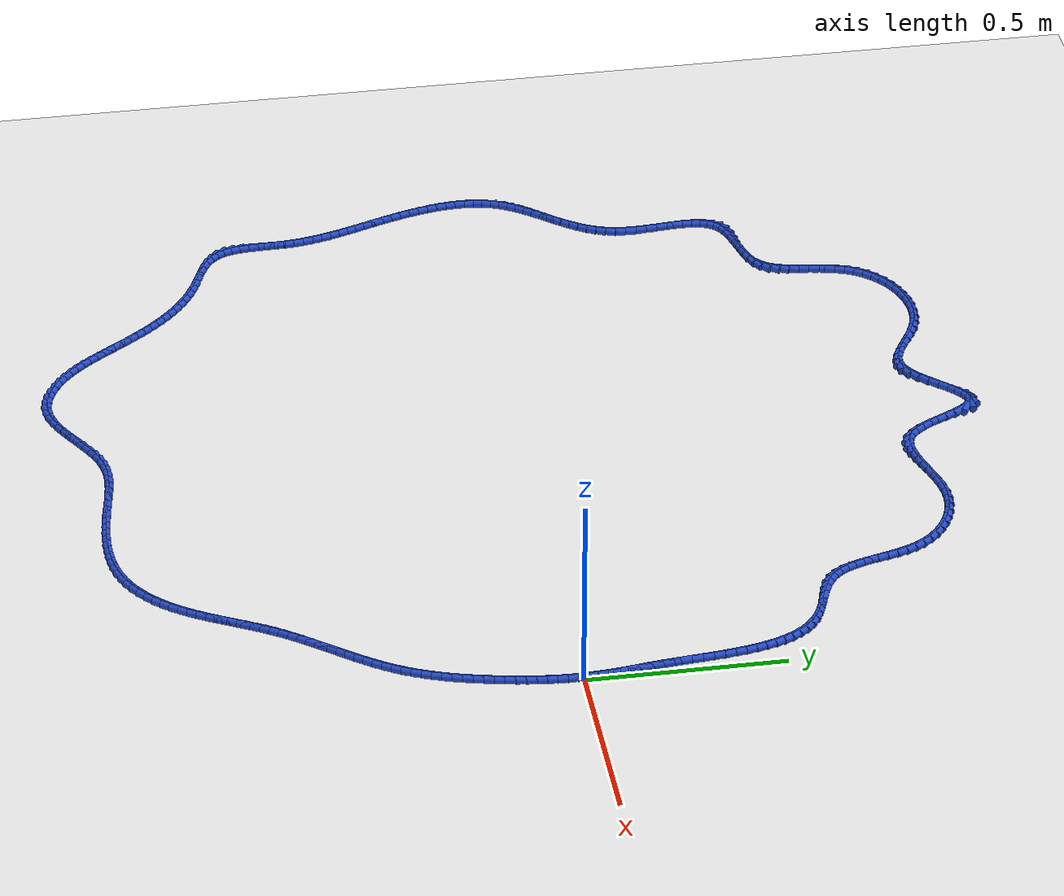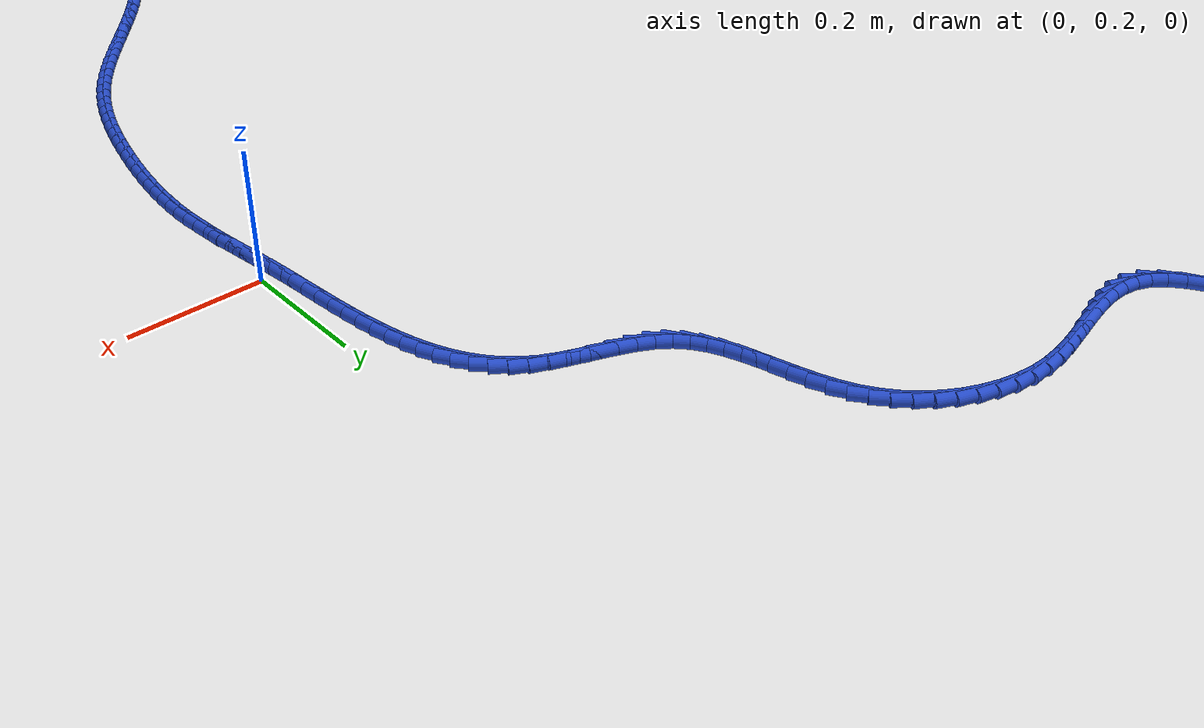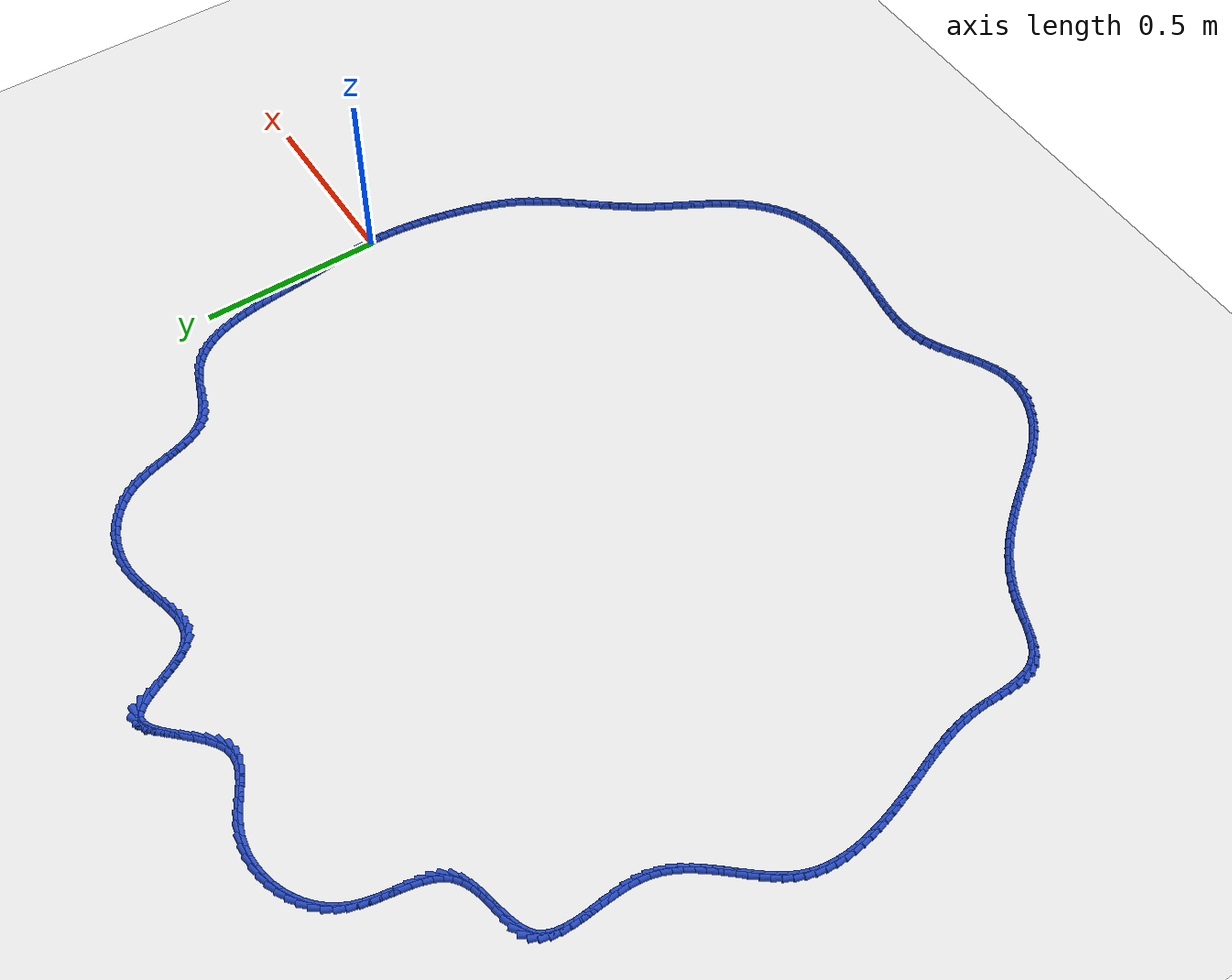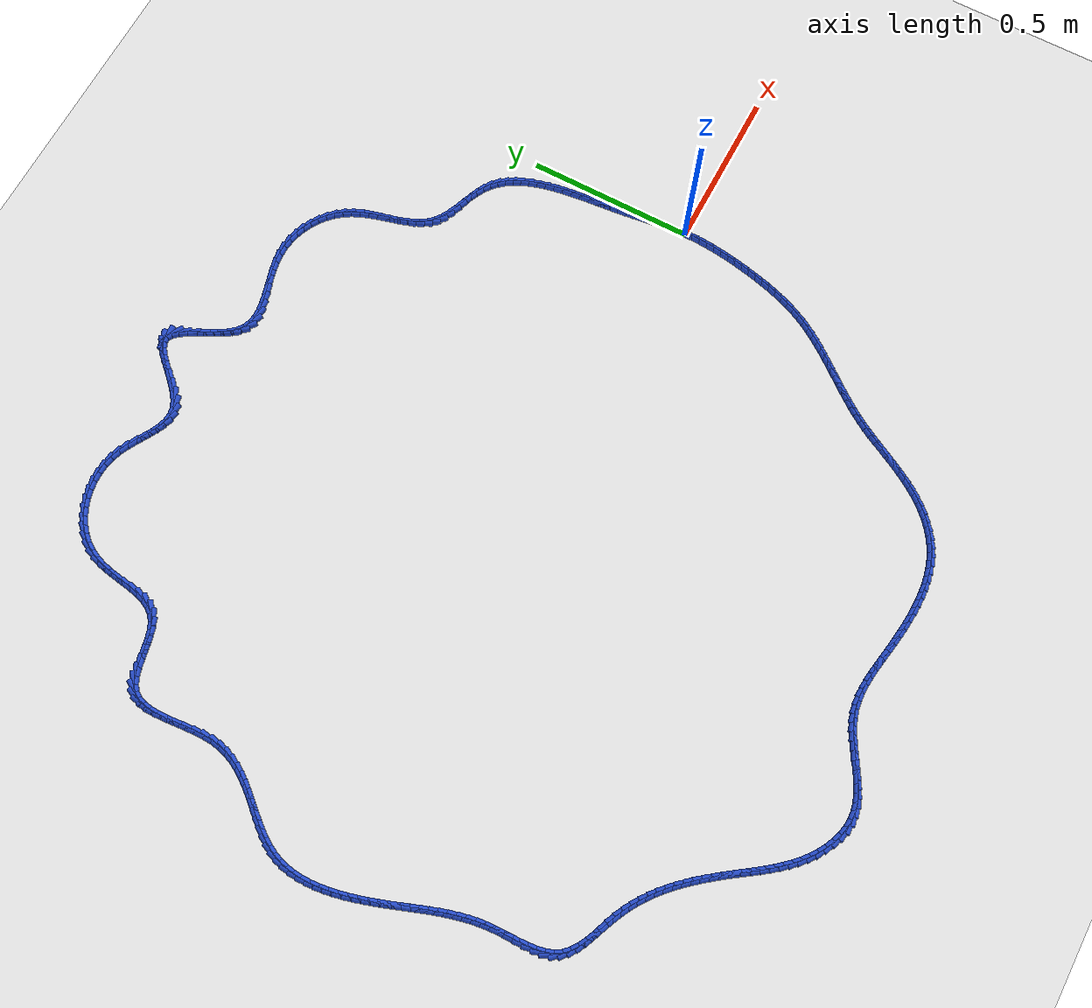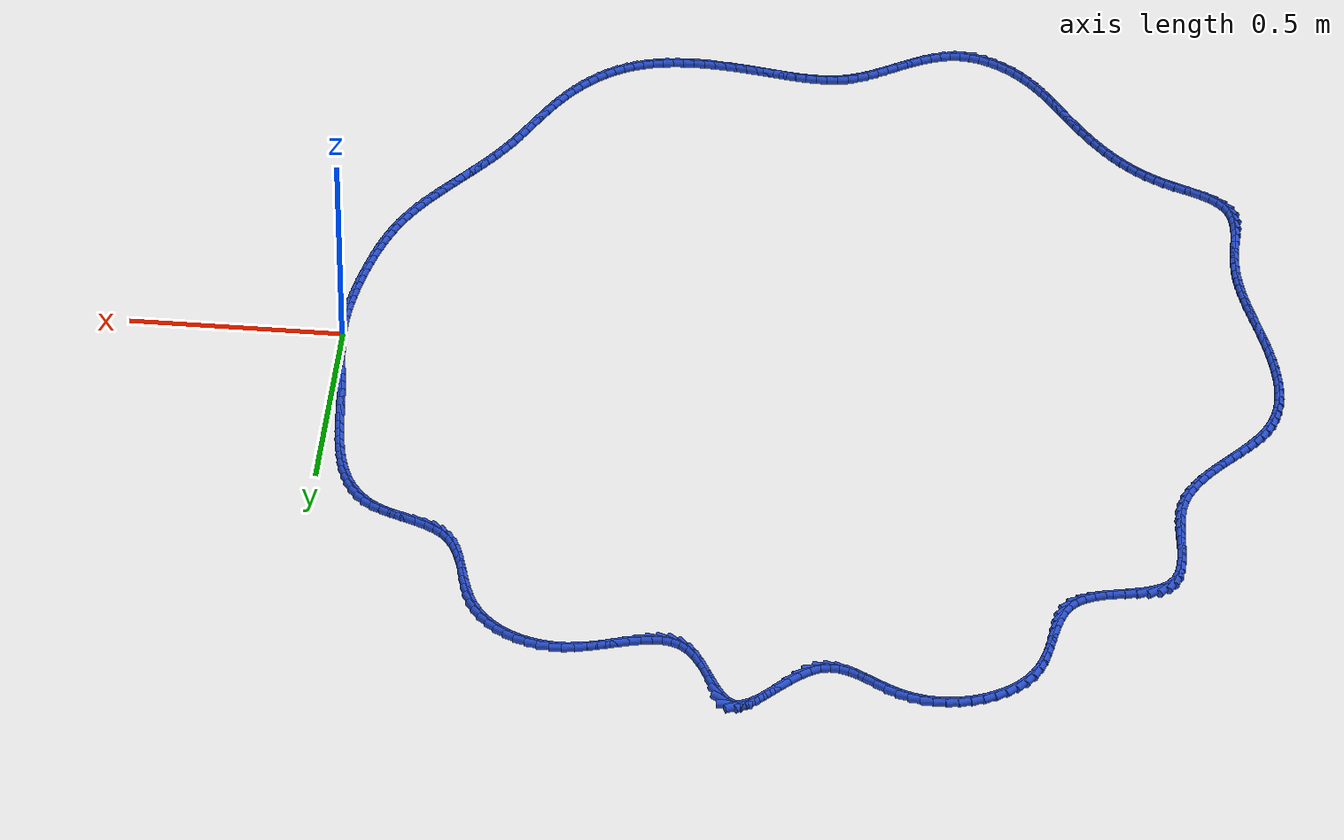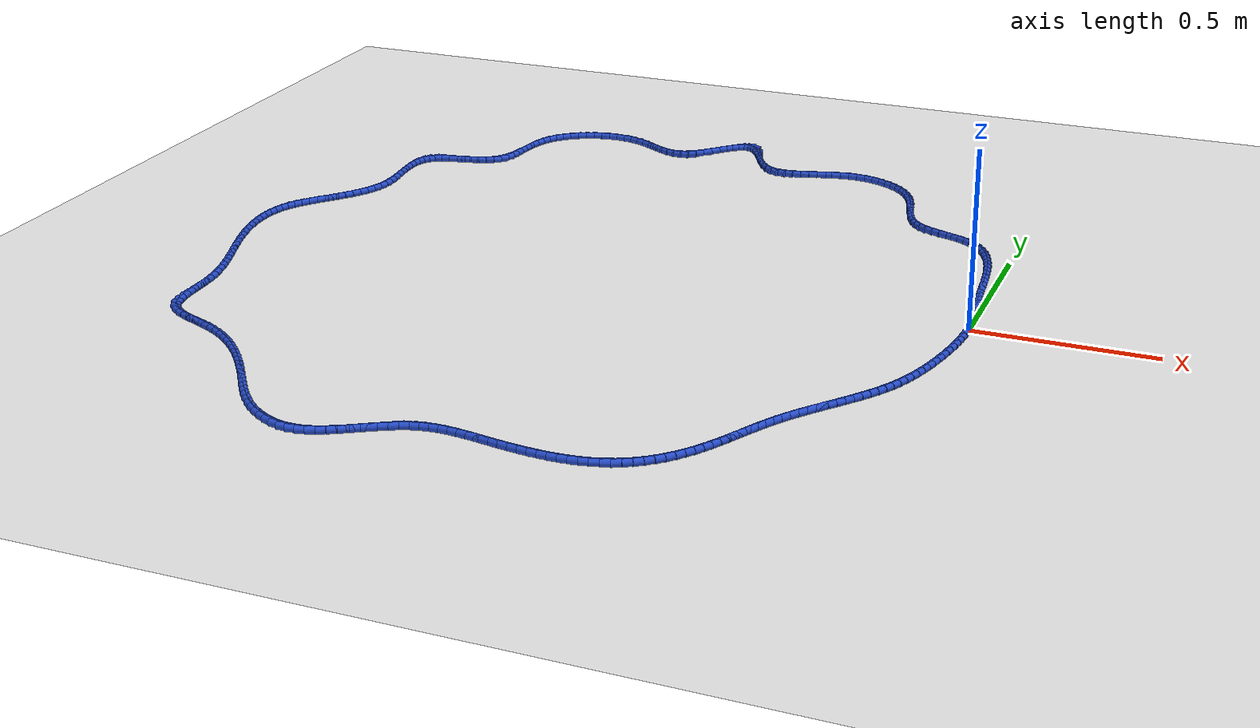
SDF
<sdf version="1.6">
 <world name="default">
  <light name="sun" type="directional">
   <pose>0 0 10 0 -0 0</pose>
   <diffuse>0.8 0.8 0.8 1</diffuse>
   <specular>0.2 0.2 0.2 1</specular>
   <attenuation>
    <range>1000</range>
    <constant>0.9</constant>
    <linear>0.01</linear>
    <quadratic>0.001</quadratic>
   </attenuation>
   <direction>-0.5 0.1 -0.9</direction>
  </light>
  <model name="ground_plane">
   <static>1</static>
   <link name="link">
    <collision name="collision">
     <geometry><plane><normal>0 0 1</normal><size>100 100</size></plane></geometry>
     <surface><friction><ode><mu>100</mu><mu2>50</mu2></ode></friction></surface>
    </collision>
    <visual name="visual">
     <cast_shadows>0</cast_shadows>
     <geometry><plane><normal>0 0 1</normal><size>100 100</size></plane></geometry>
     <material>
      <script><uri>file://media/materials/scripts/gazebo.material</uri><name>Gazebo/WhiteGlow</name></script>
     </material>
    </visual>
   </link>
  </model>
  <gravity>0 0 -9.8</gravity>
  <magnetic_field>6e-06 2.3e-05 -4.2e-05</magnetic_field>
  <atmosphere type="adiabatic"/>
  <physics name="default_physics" default="0" type="ode">
   <max_step_size>0.001</max_step_size>
   <real_time_factor>1</real_time_factor>
   <real_time_update_rate>1000</real_time_update_rate>
  </physics>
  <scene><ambient>0.4 0.4 0.4 1</ambient><background>0.7 0.7 0.7 1</background><shadows>1</shadows></scene>
  <spherical_coordinates>
   <surface_model>EARTH_WGS84</surface_model>
   <latitude_deg>0</latitude_deg>
   <longitude_deg>0</longitude_deg>
   <elevation>0</elevation>
   <heading_deg>0</heading_deg>
  </spherical_coordinates>
  <model name="line">
   <link name="link_0">
    <pose>7.806255641895632e-18 -2.7755575615628914e-17 0.01 0 1.57 -1.5297292632411528</pose>
    <collision name="collision">
     <geometry><cylinder><radius>0.01</radius><length>0.08</length></cylinder></geometry>
    </collision>
    <visual name="visual">
     <material>
      <script><name>Gazebo/Blue</name><uri>file://media/materials/scripts/gazebo.material</uri></script>
     </material>
     <geometry><cylinder><radius>0.01</radius><length>0.08</length></cylinder></geometry>
    </visual>
   </link>
   <link name="link_1">
    <pose>-0.0010044196598593667 0.02444428349632678 0.01 0 1.57 -1.4977805838000642</pose>
    <collision name="collision">
     <geometry><cylinder><radius>0.01</radius><length>0.08</length></cylinder></geometry>
    </collision>
    <visual name="visual">
     <material>
      <script><name>Gazebo/Blue</name><uri>file://media/materials/scripts/gazebo.material</uri></script>
     </material>
     <geometry><cylinder><radius>0.01</radius><length>0.08</length></cylinder></geometry>
    </visual>
   </link>
   <link name="link_2">
    <pose>-0.0027856121124592514 0.04879555210935649 0.01 0 1.57 -1.4722192824239795</pose>
    <collision name="collision">
     <geometry><cylinder><radius>0.01</radius><length>0.08</length></cylinder></geometry>
    </collision>
    <visual name="visual">
     <material>
      <script><name>Gazebo/Blue</name><uri>file://media/materials/scripts/gazebo.material</uri></script>
     </material>
     <geometry><cylinder><radius>0.01</radius><length>0.08</length></cylinder></geometry>
    </visual>
   </link>
   <link name="link_3">
    <pose>-0.0051945439665090805 0.07315339253003382 0.01 0 1.57 -1.4533037549861612</pose>
    <collision name="collision">
     <geometry><cylinder><radius>0.01</radius><length>0.08</length></cylinder></geometry>
    </collision>
    <visual name="visual">
     <material>
      <script><name>Gazebo/Blue</name><uri>file://media/materials/scripts/gazebo.material</uri></script>
     </material>
     <geometry><cylinder><radius>0.01</radius><length>0.08</length></cylinder></geometry>
    </visual>
   </link>
   <link name="link_4">
    <pose>-0.008082181830718288 0.09761739144930345 0.01 0 1.57 -1.4411130099828349</pose>
    <collision name="collision">
     <geometry><cylinder><radius>0.01</radius><length>0.08</length></cylinder></geometry>
    </collision>
    <visual name="visual">
     <material>
      <script><name>Gazebo/Blue</name><uri>file://media/materials/scripts/gazebo.material</uri></script>
     </material>
     <geometry><cylinder><radius>0.01</radius><length>0.08</length></cylinder></geometry>
    </visual>
   </link>
   <link name="link_5">
    <pose>-0.011299492313796313 0.12228713555811013 0.01 0 1.57 -1.4355729739126433</pose>
    <collision name="collision">
     <geometry><cylinder><radius>0.01</radius><length>0.08</length></cylinder></geometry>
    </collision>
    <visual name="visual">
     <material>
      <script><name>Gazebo/Blue</name><uri>file://media/materials/scripts/gazebo.material</uri></script>
     </material>
     <geometry><cylinder><radius>0.01</radius><length>0.08</length></cylinder></geometry>
    </visual>
   </link>
   <link name="link_6">
    <pose>-0.014697442024452594 0.14726221154739857 0.01 0 1.57 -1.4364815963204869</pose>
    <collision name="collision">
     <geometry><cylinder><radius>0.01</radius><length>0.08</length></cylinder></geometry>
    </collision>
    <visual name="visual">
     <material>
      <script><name>Gazebo/Blue</name><uri>file://media/materials/scripts/gazebo.material</uri></script>
     </material>
     <geometry><cylinder><radius>0.01</radius><length>0.08</length></cylinder></geometry>
    </visual>
   </link>
   <link name="link_7">
    <pose>-0.018126997571396564 0.17264220610811343 0.01 0 1.57 -1.443529939900184</pose>
    <collision name="collision">
     <geometry><cylinder><radius>0.01</radius><length>0.08</length></cylinder></geometry>
    </collision>
    <visual name="visual">
     <material>
      <script><name>Gazebo/Blue</name><uri>file://media/materials/scripts/gazebo.material</uri></script>
     </material>
     <geometry><cylinder><radius>0.01</radius><length>0.08</length></cylinder></geometry>
    </visual>
   </link>
   <link name="link_8">
    <pose>-0.02143912556333766 0.1985267059311995 0.01 0 1.57 -1.4561993239312736</pose>
    <collision name="collision">
     <geometry><cylinder><radius>0.01</radius><length>0.08</length></cylinder></geometry>
    </collision>
    <visual name="visual">
     <material>
      <script><name>Gazebo/Blue</name><uri>file://media/materials/scripts/gazebo.material</uri></script>
     </material>
     <geometry><cylinder><radius>0.01</radius><length>0.08</length></cylinder></geometry>
    </visual>
   </link>
   <link name="link_9">
    <pose>-0.0244877044674596 0.2250127570776283 0.01 0 1.57 -1.4688358760310776</pose>
    <collision name="collision">
     <geometry><cylinder><radius>0.01</radius><length>0.08</length></cylinder></geometry>
    </collision>
    <visual name="visual">
     <material>
      <script><name>Gazebo/Blue</name><uri>file://media/materials/scripts/gazebo.material</uri></script>
     </material>
     <geometry><cylinder><radius>0.01</radius><length>0.08</length></cylinder></geometry>
    </visual>
   </link>
   <link name="link_10">
    <pose>-0.02725743035437596 0.2520832657464158 0.01 0 1.57 -1.4744268627343922</pose>
    <collision name="collision">
     <geometry><cylinder><radius>0.01</radius><length>0.08</length></cylinder></geometry>
    </collision>
    <visual name="visual">
     <material>
      <script><name>Gazebo/Blue</name><uri>file://media/materials/scripts/gazebo.material</uri></script>
     </material>
     <geometry><cylinder><radius>0.01</radius><length>0.08</length></cylinder></geometry>
    </visual>
   </link>
   <link name="link_11">
    <pose>-0.02991389560781347 0.2795633040250696 0.01 0 1.57 -1.4728524655159088</pose>
    <collision name="collision">
     <geometry><cylinder><radius>0.01</radius><length>0.08</length></cylinder></geometry>
    </collision>
    <visual name="visual">
     <material>
      <script><name>Gazebo/Blue</name><uri>file://media/materials/scripts/gazebo.material</uri></script>
     </material>
     <geometry><cylinder><radius>0.01</radius><length>0.08</length></cylinder></geometry>
    </visual>
   </link>
   <link name="link_12">
    <pose>-0.03263595121667241 0.30726637571575494 0.01 0 1.57 -1.4642603872386086</pose>
    <collision name="collision">
     <geometry><cylinder><radius>0.01</radius><length>0.08</length></cylinder></geometry>
    </collision>
    <visual name="visual">
     <material>
      <script><name>Gazebo/Blue</name><uri>file://media/materials/scripts/gazebo.material</uri></script>
     </material>
     <geometry><cylinder><radius>0.01</radius><length>0.08</length></cylinder></geometry>
    </visual>
   </link>
   <link name="link_13">
    <pose>-0.03560244816985314 0.3350059846206376 0.01 0 1.57 -1.4485445015330025</pose>
    <collision name="collision">
     <geometry><cylinder><radius>0.01</radius><length>0.08</length></cylinder></geometry>
    </collision>
    <visual name="visual">
     <material>
      <script><name>Gazebo/Blue</name><uri>file://media/materials/scripts/gazebo.material</uri></script>
     </material>
     <geometry><cylinder><radius>0.01</radius><length>0.08</length></cylinder></geometry>
    </visual>
   </link>
   <link name="link_14">
    <pose>-0.03899223745625596 0.3625956345418828 0.01 0 1.57 -1.4253548308124515</pose>
    <collision name="collision">
     <geometry><cylinder><radius>0.01</radius><length>0.08</length></cylinder></geometry>
    </collision>
    <visual name="visual">
     <material>
      <script><name>Gazebo/Blue</name><uri>file://media/materials/scripts/gazebo.material</uri></script>
     </material>
     <geometry><cylinder><radius>0.01</radius><length>0.08</length></cylinder></geometry>
    </visual>
   </link>
   <link name="link_15">
    <pose>-0.042984170064781176 0.3898488292816563 0.01 0 1.57 -1.3940994646620324</pose>
    <collision name="collision">
     <geometry><cylinder><radius>0.01</radius><length>0.08</length></cylinder></geometry>
    </collision>
    <visual name="visual">
     <material>
      <script><name>Gazebo/Blue</name><uri>file://media/materials/scripts/gazebo.material</uri></script>
     </material>
     <geometry><cylinder><radius>0.01</radius><length>0.08</length></cylinder></geometry>
    </visual>
   </link>
   <link name="link_16">
    <pose>-0.04775709698432912 0.4165790726421235 0.01 0 1.57 -1.3539455619849068</pose>
    <collision name="collision">
     <geometry><cylinder><radius>0.01</radius><length>0.08</length></cylinder></geometry>
    </collision>
    <visual name="visual">
     <material>
      <script><name>Gazebo/Blue</name><uri>file://media/materials/scripts/gazebo.material</uri></script>
     </material>
     <geometry><cylinder><radius>0.01</radius><length>0.08</length></cylinder></geometry>
    </visual>
   </link>
   <link name="link_17">
    <pose>-0.0534898692038001 0.4425998684254496 0.01 0 1.57 -1.3038317987262238</pose>
    <collision name="collision">
     <geometry><cylinder><radius>0.01</radius><length>0.08</length></cylinder></geometry>
    </collision>
    <visual name="visual">
     <material>
      <script><name>Gazebo/Blue</name><uri>file://media/materials/scripts/gazebo.material</uri></script>
     </material>
     <geometry><cylinder><radius>0.01</radius><length>0.08</length></cylinder></geometry>
    </visual>
   </link>
   <link name="link_18">
    <pose>-0.06036133771209445 0.46772472043380064 0.01 0 1.57 -1.2425137462077063</pose>
    <collision name="collision">
     <geometry><cylinder><radius>0.01</radius><length>0.08</length></cylinder></geometry>
    </collision>
    <visual name="visual">
     <material>
      <script><name>Gazebo/Blue</name><uri>file://media/materials/scripts/gazebo.material</uri></script>
     </material>
     <geometry><cylinder><radius>0.01</radius><length>0.08</length></cylinder></geometry>
    </visual>
   </link>
   <link name="link_19">
    <pose>-0.06855035349811245 0.49176713246934156 0.01 0 1.57 -1.1686770045527295</pose>
    <collision name="collision">
     <geometry><cylinder><radius>0.01</radius><length>0.08</length></cylinder></geometry>
    </collision>
    <visual name="visual">
     <material>
      <script><name>Gazebo/Blue</name><uri>file://media/materials/scripts/gazebo.material</uri></script>
     </material>
     <geometry><cylinder><radius>0.01</radius><length>0.08</length></cylinder></geometry>
    </visual>
   </link>
   <link name="link_20">
    <pose>-0.07823576755075445 0.5145406083342383 0.01 0 1.57 -1.0811662777695434</pose>
    <collision name="collision">
     <geometry><cylinder><radius>0.01</radius><length>0.08</length></cylinder></geometry>
    </collision>
    <visual name="visual">
     <material>
      <script><name>Gazebo/Blue</name><uri>file://media/materials/scripts/gazebo.material</uri></script>
     </material>
     <geometry><cylinder><radius>0.01</radius><length>0.08</length></cylinder></geometry>
    </visual>
   </link>
   <link name="link_21">
    <pose>-0.0895964308589208 0.5358586518306561 0.01 0 1.57 -0.9793761368505984</pose>
    <collision name="collision">
     <geometry><cylinder><radius>0.01</radius><length>0.08</length></cylinder></geometry>
    </collision>
    <visual name="visual">
     <material>
      <script><name>Gazebo/Blue</name><uri>file://media/materials/scripts/gazebo.material</uri></script>
     </material>
     <geometry><cylinder><radius>0.01</radius><length>0.08</length></cylinder></geometry>
    </visual>
   </link>
   <link name="link_22">
    <pose>-0.10281119441151171 0.5555347667607602 0.01 0 1.57 -0.8637971546973472</pose>
    <collision name="collision">
     <geometry><cylinder><radius>0.01</radius><length>0.08</length></cylinder></geometry>
    </collision>
    <visual name="visual">
     <material>
      <script><name>Gazebo/Blue</name><uri>file://media/materials/scripts/gazebo.material</uri></script>
     </material>
     <geometry><cylinder><radius>0.01</radius><length>0.08</length></cylinder></geometry>
    </visual>
   </link>
   <link name="link_23">
    <pose>-0.11805890919742756 0.5733824569267165 0.01 0 1.57 -0.7365743909528708</pose>
    <collision name="collision">
     <geometry><cylinder><radius>0.01</radius><length>0.08</length></cylinder></geometry>
    </collision>
    <visual name="visual">
     <material>
      <script><name>Gazebo/Blue</name><uri>file://media/materials/scripts/gazebo.material</uri></script>
     </material>
     <geometry><cylinder><radius>0.01</radius><length>0.08</length></cylinder></geometry>
    </visual>
   </link>
   <link name="link_24">
    <pose>-0.13551842620556873 0.5892152261306906 0.01 0 1.57 -0.6017796554260213</pose>
    <collision name="collision">
     <geometry><cylinder><radius>0.01</radius><length>0.08</length></cylinder></geometry>
    </collision>
    <visual name="visual">
     <material>
      <script><name>Gazebo/Blue</name><uri>file://media/materials/scripts/gazebo.material</uri></script>
     </material>
     <geometry><cylinder><radius>0.01</radius><length>0.08</length></cylinder></geometry>
    </visual>
   </link>
   <link name="link_25">
    <pose>-0.15536809744392485 0.6028470395999045 0.01 0 1.57 -0.47791307891441004</pose>
    <collision name="collision">
     <geometry><cylinder><radius>0.01</radius><length>0.08</length></cylinder></geometry>
    </collision>
    <visual name="visual">
     <material>
      <script><name>Gazebo/Blue</name><uri>file://media/materials/scripts/gazebo.material</uri></script>
     </material>
     <geometry><cylinder><radius>0.01</radius><length>0.08</length></cylinder></geometry>
    </visual>
   </link>
   <link name="link_26">
    <pose>-0.1775319438520754 0.6143270513738928 0.01 0 1.57 -0.3985733415094745</pose>
    <collision name="collision">
     <geometry><cylinder><radius>0.01</radius><length>0.08</length></cylinder></geometry>
    </collision>
    <visual name="visual">
     <material>
      <script><name>Gazebo/Blue</name><uri>file://media/materials/scripts/gazebo.material</uri></script>
     </material>
     <geometry><cylinder><radius>0.01</radius><length>0.08</length></cylinder></geometry>
    </visual>
   </link>
   <link name="link_27">
    <pose>-0.20126627155441074 0.624321874677688 0.01 0 1.57 -0.3625848382005523</pose>
    <collision name="collision">
     <geometry><cylinder><radius>0.01</radius><length>0.08</length></cylinder></geometry>
    </collision>
    <visual name="visual">
     <material>
      <script><name>Gazebo/Blue</name><uri>file://media/materials/scripts/gazebo.material</uri></script>
     </material>
     <geometry><cylinder><radius>0.01</radius><length>0.08</length></cylinder></geometry>
    </visual>
   </link>
   <link name="link_28">
    <pose>-0.22571912919185647 0.6335982322082766 0.01 0 1.57 -0.36613409223701665</pose>
    <collision name="collision">
     <geometry><cylinder><radius>0.01</radius><length>0.08</length></cylinder></geometry>
    </collision>
    <visual name="visual">
     <material>
      <script><name>Gazebo/Blue</name><uri>file://media/materials/scripts/gazebo.material</uri></script>
     </material>
     <geometry><cylinder><radius>0.01</radius><length>0.08</length></cylinder></geometry>
    </visual>
   </link>
   <link name="link_29">
    <pose>-0.25003856540533786 0.6429228466626448 0.01 0 1.57 -0.4099236502568386</pose>
    <collision name="collision">
     <geometry><cylinder><radius>0.01</radius><length>0.08</length></cylinder></geometry>
    </collision>
    <visual name="visual">
     <material>
      <script><name>Gazebo/Blue</name><uri>file://media/materials/scripts/gazebo.material</uri></script>
     </material>
     <geometry><cylinder><radius>0.01</radius><length>0.08</length></cylinder></geometry>
    </visual>
   </link>
   <link name="link_30">
    <pose>-0.2733726288357806 0.6530624407377789 0.01 0 1.57 -0.4991962111669849</pose>
    <collision name="collision">
     <geometry><cylinder><radius>0.01</radius><length>0.08</length></cylinder></geometry>
    </collision>
    <visual name="visual">
     <material>
      <script><name>Gazebo/Blue</name><uri>file://media/materials/scripts/gazebo.material</uri></script>
     </material>
     <geometry><cylinder><radius>0.01</radius><length>0.08</length></cylinder></geometry>
    </visual>
   </link>
   <link name="link_31">
    <pose>-0.29486936812411013 0.6647837371306649 0.01 0 1.57 -0.6422791448224717</pose>
    <collision name="collision">
     <geometry><cylinder><radius>0.01</radius><length>0.08</length></cylinder></geometry>
    </collision>
    <visual name="visual">
     <material>
      <script><name>Gazebo/Blue</name><uri>file://media/materials/scripts/gazebo.material</uri></script>
     </material>
     <geometry><cylinder><radius>0.01</radius><length>0.08</length></cylinder></geometry>
    </visual>
   </link>
   <link name="link_32">
    <pose>-0.31367683200368496 0.6788534584598381 0.01 0 1.57 -0.8302348601905295</pose>
    <collision name="collision">
     <geometry><cylinder><radius>0.01</radius><length>0.08</length></cylinder></geometry>
    </collision>
    <visual name="visual">
     <material>
      <script><name>Gazebo/Blue</name><uri>file://media/materials/scripts/gazebo.material</uri></script>
     </material>
     <geometry><cylinder><radius>0.01</radius><length>0.08</length></cylinder></geometry>
    </visual>
   </link>
   <link name="link_33">
    <pose>-0.32919240892249013 0.6958267037793132 0.01 0 1.57 -0.9996487132325556</pose>
    <collision name="collision">
     <geometry><cylinder><radius>0.01</radius><length>0.08</length></cylinder></geometry>
    </collision>
    <visual name="visual">
     <material>
      <script><name>Gazebo/Blue</name><uri>file://media/materials/scripts/gazebo.material</uri></script>
     </material>
     <geometry><cylinder><radius>0.01</radius><length>0.08</length></cylinder></geometry>
    </visual>
   </link>
   <link name="link_34">
    <pose>-0.34178943127350214 0.7154302534906963 0.01 0 1.57 -1.1290181772112722</pose>
    <collision name="collision">
     <geometry><cylinder><radius>0.01</radius><length>0.08</length></cylinder></geometry>
    </collision>
    <visual name="visual">
     <material>
      <script><name>Gazebo/Blue</name><uri>file://media/materials/scripts/gazebo.material</uri></script>
     </material>
     <geometry><cylinder><radius>0.01</radius><length>0.08</length></cylinder></geometry>
    </visual>
   </link>
   <link name="link_35">
    <pose>-0.35207997817159914 0.737188255084178 0.01 0 1.57 -1.2192488491653564</pose>
    <collision name="collision">
     <geometry><cylinder><radius>0.01</radius><length>0.08</length></cylinder></geometry>
    </collision>
    <visual name="visual">
     <material>
      <script><name>Gazebo/Blue</name><uri>file://media/materials/scripts/gazebo.material</uri></script>
     </material>
     <geometry><cylinder><radius>0.01</radius><length>0.08</length></cylinder></geometry>
    </visual>
   </link>
   <link name="link_36">
    <pose>-0.36067612873165933 0.7606248560499487 0.01 0 1.57 -1.2748020730496026</pose>
    <collision name="collision">
     <geometry><cylinder><radius>0.01</radius><length>0.08</length></cylinder></geometry>
    </collision>
    <visual name="visual">
     <material>
      <script><name>Gazebo/Blue</name><uri>file://media/materials/scripts/gazebo.material</uri></script>
     </material>
     <geometry><cylinder><radius>0.01</radius><length>0.08</length></cylinder></geometry>
    </visual>
   </link>
   <link name="link_37">
    <pose>-0.3681899620685608 0.7852642038781988 0.01 0 1.57 -1.2999440185714706</pose>
    <collision name="collision">
     <geometry><cylinder><radius>0.01</radius><length>0.08</length></cylinder></geometry>
    </collision>
    <visual name="visual">
     <material>
      <script><name>Gazebo/Blue</name><uri>file://media/materials/scripts/gazebo.material</uri></script>
     </material>
     <geometry><cylinder><radius>0.01</radius><length>0.08</length></cylinder></geometry>
    </visual>
   </link>
   <link name="link_38">
    <pose>-0.37523355729718166 0.8106304460591186 0.01 0 1.57 -1.2973317037078116</pose>
    <collision name="collision">
     <geometry><cylinder><radius>0.01</radius><length>0.08</length></cylinder></geometry>
    </collision>
    <visual name="visual">
     <material>
      <script><name>Gazebo/Blue</name><uri>file://media/materials/scripts/gazebo.material</uri></script>
     </material>
     <geometry><cylinder><radius>0.01</radius><length>0.08</length></cylinder></geometry>
    </visual>
   </link>
   <link name="link_39">
    <pose>-0.38241899353240005 0.8362477300828985 0.01 0 1.57 -1.2677604752531975</pose>
    <collision name="collision">
     <geometry><cylinder><radius>0.01</radius><length>0.08</length></cylinder></geometry>
    </collision>
    <visual name="visual">
     <material>
      <script><name>Gazebo/Blue</name><uri>file://media/materials/scripts/gazebo.material</uri></script>
     </material>
     <geometry><cylinder><radius>0.01</radius><length>0.08</length></cylinder></geometry>
    </visual>
   </link>
   <link name="link_40">
    <pose>-0.39035834988909407 0.8616402034397295 0.01 0 1.57 -1.2103959692966826</pose>
    <collision name="collision">
     <geometry><cylinder><radius>0.01</radius><length>0.08</length></cylinder></geometry>
    </collision>
    <visual name="visual">
     <material>
      <script><name>Gazebo/Blue</name><uri>file://media/materials/scripts/gazebo.material</uri></script>
     </material>
     <geometry><cylinder><radius>0.01</radius><length>0.08</length></cylinder></geometry>
    </visual>
   </link>
   <link name="link_41">
    <pose>-0.3996637054821419 0.8863320136198011 0.01 0 1.57 -1.1234114097512395</pose>
    <collision name="collision">
     <geometry><cylinder><radius>0.01</radius><length>0.08</length></cylinder></geometry>
    </collision>
    <visual name="visual">
     <material>
      <script><name>Gazebo/Blue</name><uri>file://media/materials/scripts/gazebo.material</uri></script>
     </material>
     <geometry><cylinder><radius>0.01</radius><length>0.08</length></cylinder></geometry>
    </visual>
   </link>
   <link name="link_42">
    <pose>-0.4109471394264216 0.9098473081133044 0.01 0 1.57 -1.0083353014706375</pose>
    <collision name="collision">
     <geometry><cylinder><radius>0.01</radius><length>0.08</length></cylinder></geometry>
    </collision>
    <visual name="visual">
     <material>
      <script><name>Gazebo/Blue</name><uri>file://media/materials/scripts/gazebo.material</uri></script>
     </material>
     <geometry><cylinder><radius>0.01</radius><length>0.08</length></cylinder></geometry>
    </visual>
   </link>
   <link name="link_43">
    <pose>-0.42474697905533987 0.9317384997109359 0.01 0 1.57 -0.887326714442278</pose>
    <collision name="collision">
     <geometry><cylinder><radius>0.01</radius><length>0.08</length></cylinder></geometry>
    </collision>
    <visual name="visual">
     <material>
      <script><name>Gazebo/Blue</name><uri>file://media/materials/scripts/gazebo.material</uri></script>
     </material>
     <geometry><cylinder><radius>0.01</radius><length>0.08</length></cylinder></geometry>
    </visual>
   </link>
   <link name="link_44">
    <pose>-0.44105796557774185 0.9517663300715946 0.01 0 1.57 -0.7702196986375826</pose>
    <collision name="collision">
     <geometry><cylinder><radius>0.01</radius><length>0.08</length></cylinder></geometry>
    </collision>
    <visual name="visual">
     <material>
      <script><name>Gazebo/Blue</name><uri>file://media/materials/scripts/gazebo.material</uri></script>
     </material>
     <geometry><cylinder><radius>0.01</radius><length>0.08</length></cylinder></geometry>
    </visual>
   </link>
   <link name="link_45">
    <pose>-0.45963178341461025 0.9697846921382824 0.01 0 1.57 -0.6565164359457617</pose>
    <collision name="collision">
     <geometry><cylinder><radius>0.01</radius><length>0.08</length></cylinder></geometry>
    </collision>
    <visual name="visual">
     <material>
      <script><name>Gazebo/Blue</name><uri>file://media/materials/scripts/gazebo.material</uri></script>
     </material>
     <geometry><cylinder><radius>0.01</radius><length>0.08</length></cylinder></geometry>
    </visual>
   </link>
   <link name="link_46">
    <pose>-0.4802189828700937 0.9856479135032072 0.01 0 1.57 -0.5453960585127497</pose>
    <collision name="collision">
     <geometry><cylinder><radius>0.01</radius><length>0.08</length></cylinder></geometry>
    </collision>
    <visual name="visual">
     <material>
      <script><name>Gazebo/Blue</name><uri>file://media/materials/scripts/gazebo.material</uri></script>
     </material>
     <geometry><cylinder><radius>0.01</radius><length>0.08</length></cylinder></geometry>
    </visual>
   </link>
   <link name="link_47">
    <pose>-0.5025701142483407 0.9992103217585755 0.01 0 1.57 -0.4358918287051869</pose>
    <collision name="collision">
     <geometry><cylinder><radius>0.01</radius><length>0.08</length></cylinder></geometry>
    </collision>
    <visual name="visual">
     <material>
      <script><name>Gazebo/Blue</name><uri>file://media/materials/scripts/gazebo.material</uri></script>
     </material>
     <geometry><cylinder><radius>0.01</radius><length>0.08</length></cylinder></geometry>
    </visual>
   </link>
   <link name="link_48">
    <pose>-0.5264357278535002 1.0103262444965948 0.01 0 1.57 -0.3270015888923815</pose>
    <collision name="collision">
     <geometry><cylinder><radius>0.01</radius><length>0.08</length></cylinder></geometry>
    </collision>
    <visual name="visual">
     <material>
      <script><name>Gazebo/Blue</name><uri>file://media/materials/scripts/gazebo.material</uri></script>
     </material>
     <geometry><cylinder><radius>0.01</radius><length>0.08</length></cylinder></geometry>
    </visual>
   </link>
   <link name="link_49">
    <pose>-0.5515663739897203 1.0188500093094714 0.01 0 1.57 -0.21778171106188735</pose>
    <collision name="collision">
     <geometry><cylinder><radius>0.01</radius><length>0.08</length></cylinder></geometry>
    </collision>
    <visual name="visual">
     <material>
      <script><name>Gazebo/Blue</name><uri>file://media/materials/scripts/gazebo.material</uri></script>
     </material>
     <geometry><cylinder><radius>0.01</radius><length>0.08</length></cylinder></geometry>
    </visual>
   </link>
   <link name="link_50">
    <pose>-0.5777126029611501 1.024635943789413 0.01 0 1.57 -0.10743229434449983</pose>
    <collision name="collision">
     <geometry><cylinder><radius>0.01</radius><length>0.08</length></cylinder></geometry>
    </collision>
    <visual name="visual">
     <material>
      <script><name>Gazebo/Blue</name><uri>file://media/materials/scripts/gazebo.material</uri></script>
     </material>
     <geometry><cylinder><radius>0.01</radius><length>0.08</length></cylinder></geometry>
    </visual>
   </link>
   <link name="link_51">
    <pose>-0.6046249650719375 1.0275383755286263 0.01 0 1.57 0.004620740703959871</pose>
    <collision name="collision">
     <geometry><cylinder><radius>0.01</radius><length>0.08</length></cylinder></geometry>
    </collision>
    <visual name="visual">
     <material>
      <script><name>Gazebo/Blue</name><uri>file://media/materials/scripts/gazebo.material</uri></script>
     </material>
     <geometry><cylinder><radius>0.01</radius><length>0.08</length></cylinder></geometry>
    </visual>
   </link>
   <link name="link_52">
    <pose>-0.6320540106262318 1.0274116321193183 0.01 0 1.57 0.11573695629212997</pose>
    <collision name="collision">
     <geometry><cylinder><radius>0.01</radius><length>0.08</length></cylinder></geometry>
    </collision>
    <visual name="visual">
     <material>
      <script><name>Gazebo/Blue</name><uri>file://media/materials/scripts/gazebo.material</uri></script>
     </material>
     <geometry><cylinder><radius>0.01</radius><length>0.08</length></cylinder></geometry>
    </visual>
   </link>
   <link name="link_53">
    <pose>-0.6597530591175419 1.024191437483295 0.01 0 1.57 0.20262990746897866</pose>
    <collision name="collision">
     <geometry><cylinder><radius>0.01</radius><length>0.08</length></cylinder></geometry>
    </collision>
    <visual name="visual">
     <material>
      <script><name>Gazebo/Blue</name><uri>file://media/materials/scripts/gazebo.material</uri></script>
     </material>
     <geometry><cylinder><radius>0.01</radius><length>0.08</length></cylinder></geometry>
    </visual>
   </link>
   <link name="link_54">
    <pose>-0.6874984840334841 1.0184911544678272 0.01 0 1.57 0.2564060793894565</pose>
    <collision name="collision">
     <geometry><cylinder><radius>0.01</radius><length>0.08</length></cylinder></geometry>
    </collision>
    <visual name="visual">
     <material>
      <script><name>Gazebo/Blue</name><uri>file://media/materials/scripts/gazebo.material</uri></script>
     </material>
     <geometry><cylinder><radius>0.01</radius><length>0.08</length></cylinder></geometry>
    </visual>
   </link>
   <link name="link_55">
    <pose>-0.7150780990979356 1.0112604151744806 0.01 0 1.57 0.2795644236519791</pose>
    <collision name="collision">
     <geometry><cylinder><radius>0.01</radius><length>0.08</length></cylinder></geometry>
    </collision>
    <visual name="visual">
     <material>
      <script><name>Gazebo/Blue</name><uri>file://media/materials/scripts/gazebo.material</uri></script>
     </material>
     <geometry><cylinder><radius>0.01</radius><length>0.08</length></cylinder></geometry>
    </visual>
   </link>
   <link name="link_56">
    <pose>-0.742279800471208 1.0034512748049902 0.01 0 1.57 0.2724585727655352</pose>
    <collision name="collision">
     <geometry><cylinder><radius>0.01</radius><length>0.08</length></cylinder></geometry>
    </collision>
    <visual name="visual">
     <material>
      <script><name>Gazebo/Blue</name><uri>file://media/materials/scripts/gazebo.material</uri></script>
     </material>
     <geometry><cylinder><radius>0.01</radius><length>0.08</length></cylinder></geometry>
    </visual>
   </link>
   <link name="link_57">
    <pose>-0.7688914843136125 0.9960157885610905 0.01 0 1.57 0.23244635598275726</pose>
    <collision name="collision">
     <geometry><cylinder><radius>0.01</radius><length>0.08</length></cylinder></geometry>
    </collision>
    <visual name="visual">
     <material>
      <script><name>Gazebo/Blue</name><uri>file://media/materials/scripts/gazebo.material</uri></script>
     </material>
     <geometry><cylinder><radius>0.01</radius><length>0.08</length></cylinder></geometry>
    </visual>
   </link>
   <link name="link_58">
    <pose>-0.7947010467854609 0.989906011644517 0.01 0 1.57 0.15333261369806758</pose>
    <collision name="collision">
     <geometry><cylinder><radius>0.01</radius><length>0.08</length></cylinder></geometry>
    </collision>
    <visual name="visual">
     <material>
      <script><name>Gazebo/Blue</name><uri>file://media/materials/scripts/gazebo.material</uri></script>
     </material>
     <geometry><cylinder><radius>0.01</radius><length>0.08</length></cylinder></geometry>
    </visual>
   </link>
   <link name="link_59">
    <pose>-0.8194963840470649 0.9860739992570043 0.01 0 1.57 0.025544633148398773</pose>
    <collision name="collision">
     <geometry><cylinder><radius>0.01</radius><length>0.08</length></cylinder></geometry>
    </collision>
    <visual name="visual">
     <material>
      <script><name>Gazebo/Blue</name><uri>file://media/materials/scripts/gazebo.material</uri></script>
     </material>
     <geometry><cylinder><radius>0.01</radius><length>0.08</length></cylinder></geometry>
    </visual>
   </link>
   <link name="link_60">
    <pose>-0.8430653922587361 0.9854718066002872 0.01 0 1.57 -0.16036383075150487</pose>
    <collision name="collision">
     <geometry><cylinder><radius>0.01</radius><length>0.08</length></cylinder></geometry>
    </collision>
    <visual name="visual">
     <material>
      <script><name>Gazebo/Blue</name><uri>file://media/materials/scripts/gazebo.material</uri></script>
     </material>
     <geometry><cylinder><radius>0.01</radius><length>0.08</length></cylinder></geometry>
    </visual>
   </link>
   <link name="link_61">
    <pose>-0.8651959675807865 0.9890514888761013 0.01 0 1.57 -0.4022674501179532</pose>
    <collision name="collision">
     <geometry><cylinder><radius>0.01</radius><length>0.08</length></cylinder></geometry>
    </collision>
    <visual name="visual">
     <material>
      <script><name>Gazebo/Blue</name><uri>file://media/materials/scripts/gazebo.material</uri></script>
     </material>
     <geometry><cylinder><radius>0.01</radius><length>0.08</length></cylinder></geometry>
    </visual>
   </link>
   <link name="link_62">
    <pose>-0.8856760061735269 0.9977651012861808 0.01 0 1.57 -0.6698274395557087</pose>
    <collision name="collision">
     <geometry><cylinder><radius>0.01</radius><length>0.08</length></cylinder></geometry>
    </collision>
    <visual name="visual">
     <material>
      <script><name>Gazebo/Blue</name><uri>file://media/materials/scripts/gazebo.material</uri></script>
     </material>
     <geometry><cylinder><radius>0.01</radius><length>0.08</length></cylinder></geometry>
    </visual>
   </link>
   <link name="link_63">
    <pose>-0.9043033965153783 1.012517497872306 0.01 0 1.57 -0.8807088605219451</pose>
    <collision name="collision">
     <geometry><cylinder><radius>0.01</radius><length>0.08</length></cylinder></geometry>
    </collision>
    <visual name="visual">
     <material>
      <script><name>Gazebo/Blue</name><uri>file://media/materials/scripts/gazebo.material</uri></script>
     </material>
     <geometry><cylinder><radius>0.01</radius><length>0.08</length></cylinder></geometry>
    </visual>
   </link>
   <link name="link_64">
    <pose>-0.9211489357197618 1.0329243819512868 0.01 0 1.57 -1.0042645143305684</pose>
    <collision name="collision">
     <geometry><cylinder><radius>0.01</radius><length>0.08</length></cylinder></geometry>
    </collision>
    <visual name="visual">
     <material>
      <script><name>Gazebo/Blue</name><uri>file://media/materials/scripts/gazebo.material</uri></script>
     </material>
     <geometry><cylinder><radius>0.01</radius><length>0.08</length></cylinder></geometry>
    </visual>
   </link>
   <link name="link_65">
    <pose>-0.9365826563506443 1.0571879449589177 0.01 0 1.57 -1.0688442923768795</pose>
    <collision name="collision">
     <geometry><cylinder><radius>0.01</radius><length>0.08</length></cylinder></geometry>
    </collision>
    <visual name="visual">
     <material>
      <script><name>Gazebo/Blue</name><uri>file://media/materials/scripts/gazebo.material</uri></script>
     </material>
     <geometry><cylinder><radius>0.01</radius><length>0.08</length></cylinder></geometry>
    </visual>
   </link>
   <link name="link_66">
    <pose>-0.9509898626561805 1.0834382387933685 0.01 0 1.57 -1.0896330163368833</pose>
    <collision name="collision">
     <geometry><cylinder><radius>0.01</radius><length>0.08</length></cylinder></geometry>
    </collision>
    <visual name="visual">
     <material>
      <script><name>Gazebo/Blue</name><uri>file://media/materials/scripts/gazebo.material</uri></script>
     </material>
     <geometry><cylinder><radius>0.01</radius><length>0.08</length></cylinder></geometry>
    </visual>
   </link>
   <link name="link_67">
    <pose>-0.9647558588845252 1.1098053153528085 0.01 0 1.57 -1.0688131941317225</pose>
    <collision name="collision">
     <geometry><cylinder><radius>0.01</radius><length>0.08</length></cylinder></geometry>
    </collision>
    <visual name="visual">
     <material>
      <script><name>Gazebo/Blue</name><uri>file://media/materials/scripts/gazebo.material</uri></script>
     </material>
     <geometry><cylinder><radius>0.01</radius><length>0.08</length></cylinder></geometry>
    </visual>
   </link>
   <link name="link_68">
    <pose>-0.9782659492838334 1.1344192265354078 0.01 0 1.57 -0.9945728217207903</pose>
    <collision name="collision">
     <geometry><cylinder><radius>0.01</radius><length>0.08</length></cylinder></geometry>
    </collision>
    <visual name="visual">
     <material>
      <script><name>Gazebo/Blue</name><uri>file://media/materials/scripts/gazebo.material</uri></script>
     </material>
     <geometry><cylinder><radius>0.01</radius><length>0.08</length></cylinder></geometry>
    </visual>
   </link>
   <link name="link_69">
    <pose>-0.9919054381022597 1.1554100242393353 0.01 0 1.57 -0.8306777261333411</pose>
    <collision name="collision">
     <geometry><cylinder><radius>0.01</radius><length>0.08</length></cylinder></geometry>
    </collision>
    <visual name="visual">
     <material>
      <script><name>Gazebo/Blue</name><uri>file://media/materials/scripts/gazebo.material</uri></script>
     </material>
     <geometry><cylinder><radius>0.01</radius><length>0.08</length></cylinder></geometry>
    </visual>
   </link>
   <link name="link_70">
    <pose>-1.006059629587959 1.1709077603627605 0.01 0 1.57 -0.49541399150802545</pose>
    <collision name="collision">
     <geometry><cylinder><radius>0.01</radius><length>0.08</length></cylinder></geometry>
    </collision>
    <visual name="visual">
     <material>
      <script><name>Gazebo/Blue</name><uri>file://media/materials/scripts/gazebo.material</uri></script>
     </material>
     <geometry><cylinder><radius>0.01</radius><length>0.08</length></cylinder></geometry>
    </visual>
   </link>
   <link name="link_71">
    <pose>-1.0211138279890861 1.1790424868038534 0.01 0 1.57 0.04532884184617204</pose>
    <collision name="collision">
     <geometry><cylinder><radius>0.01</radius><length>0.08</length></cylinder></geometry>
    </collision>
    <visual name="visual">
     <material>
      <script><name>Gazebo/Blue</name><uri>file://media/materials/scripts/gazebo.material</uri></script>
     </material>
     <geometry><cylinder><radius>0.01</radius><length>0.08</length></cylinder></geometry>
    </visual>
   </link>
   <link name="link_72">
    <pose>-1.0374026441365822 1.178303627517824 0.01 0 1.57 0.46151249241023273</pose>
    <collision name="collision">
     <geometry><cylinder><radius>0.01</radius><length>0.08</length></cylinder></geometry>
    </collision>
    <visual name="visual">
     <material>
      <script><name>Gazebo/Blue</name><uri>file://media/materials/scripts/gazebo.material</uri></script>
     </material>
     <geometry><cylinder><radius>0.01</radius><length>0.08</length></cylinder></geometry>
    </visual>
   </link>
   <link name="link_73">
    <pose>-1.0549206282303747 1.1695913393558681 0.01 0 1.57 0.6718697735068137</pose>
    <collision name="collision">
     <geometry><cylinder><radius>0.01</radius><length>0.08</length></cylinder></geometry>
    </collision>
    <visual name="visual">
     <material>
      <script><name>Gazebo/Blue</name><uri>file://media/materials/scripts/gazebo.material</uri></script>
     </material>
     <geometry><cylinder><radius>0.01</radius><length>0.08</length></cylinder></geometry>
    </visual>
   </link>
   <link name="link_74">
    <pose>-1.0735224718287009 1.1547972547989758 0.01 0 1.57 0.7708935914080731</pose>
    <collision name="collision">
     <geometry><cylinder><radius>0.01</radius><length>0.08</length></cylinder></geometry>
    </collision>
    <visual name="visual">
     <material>
      <script><name>Gazebo/Blue</name><uri>file://media/materials/scripts/gazebo.material</uri></script>
     </material>
     <geometry><cylinder><radius>0.01</radius><length>0.08</length></cylinder></geometry>
    </visual>
   </link>
   <link name="link_75">
    <pose>-1.0930624352525116 1.1358160634239158 0.01 0 1.57 0.8080176315637548</pose>
    <collision name="collision">
     <geometry><cylinder><radius>0.01</radius><length>0.08</length></cylinder></geometry>
    </collision>
    <visual name="visual">
     <material>
      <script><name>Gazebo/Blue</name><uri>file://media/materials/scripts/gazebo.material</uri></script>
     </material>
     <geometry><cylinder><radius>0.01</radius><length>0.08</length></cylinder></geometry>
    </visual>
   </link>
   <link name="link_76">
    <pose>-1.1133947788227554 1.1145424548074574 0.01 0 1.57 0.8016299626486116</pose>
    <collision name="collision">
     <geometry><cylinder><radius>0.01</radius><length>0.08</length></cylinder></geometry>
    </collision>
    <visual name="visual">
     <material>
      <script><name>Gazebo/Blue</name><uri>file://media/materials/scripts/gazebo.material</uri></script>
     </material>
     <geometry><cylinder><radius>0.01</radius><length>0.08</length></cylinder></geometry>
    </visual>
   </link>
   <link name="link_77">
    <pose>-1.1343737628603825 1.0928711185263675 0.01 0 1.57 0.7540668357353255</pose>
    <collision name="collision">
     <geometry><cylinder><radius>0.01</radius><length>0.08</length></cylinder></geometry>
    </collision>
    <visual name="visual">
     <material>
      <script><name>Gazebo/Blue</name><uri>file://media/materials/scripts/gazebo.material</uri></script>
     </material>
     <geometry><cylinder><radius>0.01</radius><length>0.08</length></cylinder></geometry>
    </visual>
   </link>
   <link name="link_78">
    <pose>-1.1558536476863426 1.0726967441574162 0.01 0 1.57 0.6553080491785842</pose>
    <collision name="collision">
     <geometry><cylinder><radius>0.01</radius><length>0.08</length></cylinder></geometry>
    </collision>
    <visual name="visual">
     <material>
      <script><name>Gazebo/Blue</name><uri>file://media/materials/scripts/gazebo.material</uri></script>
     </material>
     <geometry><cylinder><radius>0.01</radius><length>0.08</length></cylinder></geometry>
    </visual>
   </link>
   <link name="link_79">
    <pose>-1.1776886936215845 1.0559140212773714 0.01 0 1.57 0.4807061477957808</pose>
    <collision name="collision">
     <geometry><cylinder><radius>0.01</radius><length>0.08</length></cylinder></geometry>
    </collision>
    <visual name="visual">
     <material>
      <script><name>Gazebo/Blue</name><uri>file://media/materials/scripts/gazebo.material</uri></script>
     </material>
     <geometry><cylinder><radius>0.01</radius><length>0.08</length></cylinder></geometry>
    </visual>
   </link>
   <link name="link_80">
    <pose>-1.1997331609870585 1.0444176394630023 0.01 0 1.57 0.20677118024986288</pose>
    <collision name="collision">
     <geometry><cylinder><radius>0.01</radius><length>0.08</length></cylinder></geometry>
    </collision>
    <visual name="visual">
     <material>
      <script><name>Gazebo/Blue</name><uri>file://media/materials/scripts/gazebo.material</uri></script>
     </material>
     <geometry><cylinder><radius>0.01</radius><length>0.08</length></cylinder></geometry>
    </visual>
   </link>
   <link name="link_81">
    <pose>-1.2218678625579902 1.0397744597150516 0.01 0 1.57 -0.07576717412405314</pose>
    <collision name="collision">
     <geometry><cylinder><radius>0.01</radius><length>0.08</length></cylinder></geometry>
    </collision>
    <visual name="visual">
     <material>
      <script><name>Gazebo/Blue</name><uri>file://media/materials/scripts/gazebo.material</uri></script>
     </material>
     <geometry><cylinder><radius>0.01</radius><length>0.08</length></cylinder></geometry>
    </visual>
   </link>
   <link name="link_82">
    <pose>-1.24414256292362 1.0414653877388156 0.01 0 1.57 -0.2885663111340343</pose>
    <collision name="collision">
     <geometry><cylinder><radius>0.01</radius><length>0.08</length></cylinder></geometry>
    </collision>
    <visual name="visual">
     <material>
      <script><name>Gazebo/Blue</name><uri>file://media/materials/scripts/gazebo.material</uri></script>
     </material>
     <geometry><cylinder><radius>0.01</radius><length>0.08</length></cylinder></geometry>
    </visual>
   </link>
   <link name="link_83">
    <pose>-1.2666732529106843 1.0481536702425271 0.01 0 1.57 -0.42433054549942584</pose>
    <collision name="collision">
     <geometry><cylinder><radius>0.01</radius><length>0.08</length></cylinder></geometry>
    </collision>
    <visual name="visual">
     <material>
      <script><name>Gazebo/Blue</name><uri>file://media/materials/scripts/gazebo.material</uri></script>
     </material>
     <geometry><cylinder><radius>0.01</radius><length>0.08</length></cylinder></geometry>
    </visual>
   </link>
   <link name="link_84">
    <pose>-1.2895760786914796 1.0585006359680453 0.01 0 1.57 -0.49631678908446214</pose>
    <collision name="collision">
     <geometry><cylinder><radius>0.01</radius><length>0.08</length></cylinder></geometry>
    </collision>
    <visual name="visual">
     <material>
      <script><name>Gazebo/Blue</name><uri>file://media/materials/scripts/gazebo.material</uri></script>
     </material>
     <geometry><cylinder><radius>0.01</radius><length>0.08</length></cylinder></geometry>
    </visual>
   </link>
   <link name="link_85">
    <pose>-1.312967186438303 1.0711676136572317 0.01 0 1.57 -0.5171515503069973</pose>
    <collision name="collision">
     <geometry><cylinder><radius>0.01</radius><length>0.08</length></cylinder></geometry>
    </collision>
    <visual name="visual">
     <material>
      <script><name>Gazebo/Blue</name><uri>file://media/materials/scripts/gazebo.material</uri></script>
     </material>
     <geometry><cylinder><radius>0.01</radius><length>0.08</length></cylinder></geometry>
    </visual>
   </link>
   <link name="link_86">
    <pose>-1.336962722323453 1.0848159320519464 0.01 0 1.57 -0.4933864481368131</pose>
    <collision name="collision">
     <geometry><cylinder><radius>0.01</radius><length>0.08</length></cylinder></geometry>
    </collision>
    <visual name="visual">
     <material>
      <script><name>Gazebo/Blue</name><uri>file://media/materials/scripts/gazebo.material</uri></script>
     </material>
     <geometry><cylinder><radius>0.01</radius><length>0.08</length></cylinder></geometry>
    </visual>
   </link>
   <link name="link_87">
    <pose>-1.3616788325192264 1.0981069198940505 0.01 0 1.57 -0.42598067674768475</pose>
    <collision name="collision">
     <geometry><cylinder><radius>0.01</radius><length>0.08</length></cylinder></geometry>
    </collision>
    <visual name="visual">
     <material>
      <script><name>Gazebo/Blue</name><uri>file://media/materials/scripts/gazebo.material</uri></script>
     </material>
     <geometry><cylinder><radius>0.01</radius><length>0.08</length></cylinder></geometry>
    </visual>
   </link>
   <link name="link_88">
    <pose>-1.38723166319792 1.1097019059254034 0.01 0 1.57 -0.3148389586312084</pose>
    <collision name="collision">
     <geometry><cylinder><radius>0.01</radius><length>0.08</length></cylinder></geometry>
    </collision>
    <visual name="visual">
     <material>
      <script><name>Gazebo/Blue</name><uri>file://media/materials/scripts/gazebo.material</uri></script>
     </material>
     <geometry><cylinder><radius>0.01</radius><length>0.08</length></cylinder></geometry>
    </visual>
   </link>
   <link name="link_89">
    <pose>-1.4137160454654953 1.1183271094655975 0.01 0 1.57 -0.18885814545173493</pose>
    <collision name="collision">
     <geometry><cylinder><radius>0.01</radius><length>0.08</length></cylinder></geometry>
    </collision>
    <visual name="visual">
     <material>
      <script><name>Gazebo/Blue</name><uri>file://media/materials/scripts/gazebo.material</uri></script>
     </material>
     <geometry><cylinder><radius>0.01</radius><length>0.08</length></cylinder></geometry>
    </visual>
   </link>
   <link name="link_90">
    <pose>-1.4409558598700893 1.1235336188708063 0.01 0 1.57 -0.06888871842945583</pose>
    <collision name="collision">
     <geometry><cylinder><radius>0.01</radius><length>0.08</length></cylinder></geometry>
    </collision>
    <visual name="visual">
     <material>
      <script><name>Gazebo/Blue</name><uri>file://media/materials/scripts/gazebo.material</uri></script>
     </material>
     <geometry><cylinder><radius>0.01</radius><length>0.08</length></cylinder></geometry>
    </visual>
   </link>
   <link name="link_91">
    <pose>-1.46858851334749 1.1254402139247506 0.01 0 1.57 0.0456436814741091</pose>
    <collision name="collision">
     <geometry><cylinder><radius>0.01</radius><length>0.08</length></cylinder></geometry>
    </collision>
    <visual name="visual">
     <material>
      <script><name>Gazebo/Blue</name><uri>file://media/materials/scripts/gazebo.material</uri></script>
     </material>
     <geometry><cylinder><radius>0.01</radius><length>0.08</length></cylinder></geometry>
    </visual>
   </link>
   <link name="link_92">
    <pose>-1.4962477360878363 1.12417686772135 0.01 0 1.57 0.15623420661126494</pose>
    <collision name="collision">
     <geometry><cylinder><radius>0.01</radius><length>0.08</length></cylinder></geometry>
    </collision>
    <visual name="visual">
     <material>
      <script><name>Gazebo/Blue</name><uri>file://media/materials/scripts/gazebo.material</uri></script>
     </material>
     <geometry><cylinder><radius>0.01</radius><length>0.08</length></cylinder></geometry>
    </visual>
   </link>
   <link name="link_93">
    <pose>-1.5235672582812674 1.1198735533545239 0.01 0 1.57 0.2646799480104185</pose>
    <collision name="collision">
     <geometry><cylinder><radius>0.01</radius><length>0.08</length></cylinder></geometry>
    </collision>
    <visual name="visual">
     <material>
      <script><name>Gazebo/Blue</name><uri>file://media/materials/scripts/gazebo.material</uri></script>
     </material>
     <geometry><cylinder><radius>0.01</radius><length>0.08</length></cylinder></geometry>
    </visual>
   </link>
   <link name="link_94">
    <pose>-1.5501808101179215 1.1126602439181914 0.01 0 1.57 0.3729505459480875</pose>
    <collision name="collision">
     <geometry><cylinder><radius>0.01</radius><length>0.08</length></cylinder></geometry>
    </collision>
    <visual name="visual">
     <material>
      <script><name>Gazebo/Blue</name><uri>file://media/materials/scripts/gazebo.material</uri></script>
     </material>
     <geometry><cylinder><radius>0.01</radius><length>0.08</length></cylinder></geometry>
    </visual>
   </link>
   <link name="link_95">
    <pose>-1.575722121787937 1.1026669125062722 0.01 0 1.57 0.4831024863905607</pose>
    <collision name="collision">
     <geometry><cylinder><radius>0.01</radius><length>0.08</length></cylinder></geometry>
    </collision>
    <visual name="visual">
     <material>
      <script><name>Gazebo/Blue</name><uri>file://media/materials/scripts/gazebo.material</uri></script>
     </material>
     <geometry><cylinder><radius>0.01</radius><length>0.08</length></cylinder></geometry>
    </visual>
   </link>
   <link name="link_96">
    <pose>-1.5998249234814534 1.0900235322126854 0.01 0 1.57 0.5972012273908236</pose>
    <collision name="collision">
     <geometry><cylinder><radius>0.01</radius><length>0.08</length></cylinder></geometry>
    </collision>
    <visual name="visual">
     <material>
      <script><name>Gazebo/Blue</name><uri>file://media/materials/scripts/gazebo.material</uri></script>
     </material>
     <geometry><cylinder><radius>0.01</radius><length>0.08</length></cylinder></geometry>
    </visual>
   </link>
   <link name="link_97">
    <pose>-1.622122945388608 1.07486007613135 0.01 0 1.57 0.717208475605132</pose>
    <collision name="collision">
     <geometry><cylinder><radius>0.01</radius><length>0.08</length></cylinder></geometry>
    </collision>
    <visual name="visual">
     <material>
      <script><name>Gazebo/Blue</name><uri>file://media/materials/scripts/gazebo.material</uri></script>
     </material>
     <geometry><cylinder><radius>0.01</radius><length>0.08</length></cylinder></geometry>
    </visual>
   </link>
   <link name="link_98">
    <pose>-1.6422499176995402 1.057306517356186 0.01 0 1.57 0.8447891120028037</pose>
    <collision name="collision">
     <geometry><cylinder><radius>0.01</radius><length>0.08</length></cylinder></geometry>
    </collision>
    <visual name="visual">
     <material>
      <script><name>Gazebo/Blue</name><uri>file://media/materials/scripts/gazebo.material</uri></script>
     </material>
     <geometry><cylinder><radius>0.01</radius><length>0.08</length></cylinder></geometry>
    </visual>
   </link>
   <link name="link_99">
    <pose>-1.6598395706043891 1.0374928289811125 0.01 0 1.57 0.9810028139621465</pose>
    <collision name="collision">
     <geometry><cylinder><radius>0.01</radius><length>0.08</length></cylinder></geometry>
    </collision>
    <visual name="visual">
     <material>
      <script><name>Gazebo/Blue</name><uri>file://media/materials/scripts/gazebo.material</uri></script>
     </material>
     <geometry><cylinder><radius>0.01</radius><length>0.08</length></cylinder></geometry>
    </visual>
   </link>
   <link name="link_100">
    <pose>-1.6745256342932928 1.0155489841000485 0.01 0 1.57 1.1248142707986852</pose>
    <collision name="collision">
     <geometry><cylinder><radius>0.01</radius><length>0.08</length></cylinder></geometry>
    </collision>
    <visual name="visual">
     <material>
      <script><name>Gazebo/Blue</name><uri>file://media/materials/scripts/gazebo.material</uri></script>
     </material>
     <geometry><cylinder><radius>0.01</radius><length>0.08</length></cylinder></geometry>
    </visual>
   </link>
   <link name="link_101">
    <pose>-1.6859685428202678 0.9916153095414554 0.01 0 1.57 1.2518827965363</pose>
    <collision name="collision">
     <geometry><cylinder><radius>0.01</radius><length>0.08</length></cylinder></geometry>
    </collision>
    <visual name="visual">
     <material>
      <script><name>Gazebo/Blue</name><uri>file://media/materials/scripts/gazebo.material</uri></script>
     </material>
     <geometry><cylinder><radius>0.01</radius><length>0.08</length></cylinder></geometry>
    </visual>
   </link>
   <link name="link_102">
    <pose>-1.6944076263756809 0.9660565841812594 0.01 0 1.57 1.3405869892472908</pose>
    <collision name="collision">
     <geometry><cylinder><radius>0.01</radius><length>0.08</length></cylinder></geometry>
    </collision>
    <visual name="visual">
     <material>
      <script><name>Gazebo/Blue</name><uri>file://media/materials/scripts/gazebo.material</uri></script>
     </material>
     <geometry><cylinder><radius>0.01</radius><length>0.08</length></cylinder></geometry>
    </visual>
   </link>
   <link name="link_103">
    <pose>-1.700642157647981 0.9394546901584209 0.01 0 1.57 1.3933339447323774</pose>
    <collision name="collision">
     <geometry><cylinder><radius>0.01</radius><length>0.08</length></cylinder></geometry>
    </collision>
    <visual name="visual">
     <material>
      <script><name>Gazebo/Blue</name><uri>file://media/materials/scripts/gazebo.material</uri></script>
     </material>
     <geometry><cylinder><radius>0.01</radius><length>0.08</length></cylinder></geometry>
    </visual>
   </link>
   <link name="link_104">
    <pose>-1.705494321144945 0.9124003930789606 0.01 0 1.57 1.4126688868766377</pose>
    <collision name="collision">
     <geometry><cylinder><radius>0.01</radius><length>0.08</length></cylinder></geometry>
    </collision>
    <visual name="visual">
     <material>
      <script><name>Gazebo/Blue</name><uri>file://media/materials/scripts/gazebo.material</uri></script>
     </material>
     <geometry><cylinder><radius>0.01</radius><length>0.08</length></cylinder></geometry>
    </visual>
   </link>
   <link name="link_105">
    <pose>-1.7097863013743504 0.8854844585489006 0.01 0 1.57 1.3986146203841454</pose>
    <collision name="collision">
     <geometry><cylinder><radius>0.01</radius><length>0.08</length></cylinder></geometry>
    </collision>
    <visual name="visual">
     <material>
      <script><name>Gazebo/Blue</name><uri>file://media/materials/scripts/gazebo.material</uri></script>
     </material>
     <geometry><cylinder><radius>0.01</radius><length>0.08</length></cylinder></geometry>
    </visual>
   </link>
   <link name="link_106">
    <pose>-1.714340282843974 0.8592976521742615 0.01 0 1.57 1.3478323334472617</pose>
    <collision name="collision">
     <geometry><cylinder><radius>0.01</radius><length>0.08</length></cylinder></geometry>
    </collision>
    <visual name="visual">
     <material>
      <script><name>Gazebo/Blue</name><uri>file://media/materials/scripts/gazebo.material</uri></script>
     </material>
     <geometry><cylinder><radius>0.01</radius><length>0.08</length></cylinder></geometry>
    </visual>
   </link>
   <link name="link_107">
    <pose>-1.7199784500615936 0.8344307395610651 0.01 0 1.57 1.2532680598797996</pose>
    <collision name="collision">
     <geometry><cylinder><radius>0.01</radius><length>0.08</length></cylinder></geometry>
    </collision>
    <visual name="visual">
     <material>
      <script><name>Gazebo/Blue</name><uri>file://media/materials/scripts/gazebo.material</uri></script>
     </material>
     <geometry><cylinder><radius>0.01</radius><length>0.08</length></cylinder></geometry>
    </visual>
   </link>
   <link name="link_108">
    <pose>-1.7275229875349862 0.811474486315333 0.01 0 1.57 1.1053638174751952</pose>
    <collision name="collision">
     <geometry><cylinder><radius>0.01</radius><length>0.08</length></cylinder></geometry>
    </collision>
    <visual name="visual">
     <material>
      <script><name>Gazebo/Blue</name><uri>file://media/materials/scripts/gazebo.material</uri></script>
     </material>
     <geometry><cylinder><radius>0.01</radius><length>0.08</length></cylinder></geometry>
    </visual>
   </link>
   <link name="link_109">
    <pose>-1.737796079771929 0.7910196580430858 0.01 0 1.57 0.8983873534197166</pose>
    <collision name="collision">
     <geometry><cylinder><radius>0.01</radius><length>0.08</length></cylinder></geometry>
    </collision>
    <visual name="visual">
     <material>
      <script><name>Gazebo/Blue</name><uri>file://media/materials/scripts/gazebo.material</uri></script>
     </material>
     <geometry><cylinder><radius>0.01</radius><length>0.08</length></cylinder></geometry>
    </visual>
   </link>
   <link name="link_110">
    <pose>-1.7516199112801996 0.7736570203503452 0.01 0 1.57 0.6475978409784574</pose>
    <collision name="collision">
     <geometry><cylinder><radius>0.01</radius><length>0.08</length></cylinder></geometry>
    </collision>
    <visual name="visual">
     <material>
      <script><name>Gazebo/Blue</name><uri>file://media/materials/scripts/gazebo.material</uri></script>
     </material>
     <geometry><cylinder><radius>0.01</radius><length>0.08</length></cylinder></geometry>
    </visual>
   </link>
   <link name="link_111">
    <pose>-1.769760602279494 0.7599350223835242 0.01 0 1.57 0.43552371425383307</pose>
    <collision name="collision">
     <geometry><cylinder><radius>0.01</radius><length>0.08</length></cylinder></geometry>
    </collision>
    <visual name="visual">
     <material>
      <script><name>Gazebo/Blue</name><uri>file://media/materials/scripts/gazebo.material</uri></script>
     </material>
     <geometry><cylinder><radius>0.01</radius><length>0.08</length></cylinder></geometry>
    </visual>
   </link>
   <link name="link_112">
    <pose>-1.7919404203750597 0.7496142294416105 0.01 0 1.57 0.3042602289394803</pose>
    <collision name="collision">
     <geometry><cylinder><radius>0.01</radius><length>0.08</length></cylinder></geometry>
    </collision>
    <visual name="visual">
     <material>
      <script><name>Gazebo/Blue</name><uri>file://media/materials/scripts/gazebo.material</uri></script>
     </material>
     <geometry><cylinder><radius>0.01</radius><length>0.08</length></cylinder></geometry>
    </visual>
   </link>
   <link name="link_113">
    <pose>-1.816958363419927 0.741758337060064 0.01 0 1.57 0.23418600710534068</pose>
    <collision name="collision">
     <geometry><cylinder><radius>0.01</radius><length>0.08</length></cylinder></geometry>
    </collision>
    <visual name="visual">
     <material>
      <script><name>Gazebo/Blue</name><uri>file://media/materials/scripts/gazebo.material</uri></script>
     </material>
     <geometry><cylinder><radius>0.01</radius><length>0.08</length></cylinder></geometry>
    </visual>
   </link>
   <link name="link_114">
    <pose>-1.8435815955240027 0.7354070131562093 0.01 0 1.57 0.21188291376486307</pose>
    <collision name="collision">
     <geometry><cylinder><radius>0.01</radius><length>0.08</length></cylinder></geometry>
    </collision>
    <visual name="visual">
     <material>
      <script><name>Gazebo/Blue</name><uri>file://media/materials/scripts/gazebo.material</uri></script>
     </material>
     <geometry><cylinder><radius>0.01</radius><length>0.08</length></cylinder></geometry>
    </visual>
   </link>
   <link name="link_115">
    <pose>-1.8705772807971945 0.7295999256473709 0.01 0 1.57 0.23376100005304193</pose>
    <collision name="collision">
     <geometry><cylinder><radius>0.01</radius><length>0.08</length></cylinder></geometry>
    </collision>
    <visual name="visual">
     <material>
      <script><name>Gazebo/Blue</name><uri>file://media/materials/scripts/gazebo.material</uri></script>
     </material>
     <geometry><cylinder><radius>0.01</radius><length>0.08</length></cylinder></geometry>
    </visual>
   </link>
   <link name="link_116">
    <pose>-1.8967125833494087 0.7233767424508731 0.01 0 1.57 0.3061577437839099</pose>
    <collision name="collision">
     <geometry><cylinder><radius>0.01</radius><length>0.08</length></cylinder></geometry>
    </collision>
    <visual name="visual">
     <material>
      <script><name>Gazebo/Blue</name><uri>file://media/materials/scripts/gazebo.material</uri></script>
     </material>
     <geometry><cylinder><radius>0.01</radius><length>0.08</length></cylinder></geometry>
    </visual>
   </link>
   <link name="link_117">
    <pose>-1.9207546672905524 0.7157771314840409 0.01 0 1.57 0.44723262294675337</pose>
    <collision name="collision">
     <geometry><cylinder><radius>0.01</radius><length>0.08</length></cylinder></geometry>
    </collision>
    <visual name="visual">
     <material>
      <script><name>Gazebo/Blue</name><uri>file://media/materials/scripts/gazebo.material</uri></script>
     </material>
     <geometry><cylinder><radius>0.01</radius><length>0.08</length></cylinder></geometry>
    </visual>
   </link>
   <link name="link_118">
    <pose>-1.9414706967305342 0.7058407606641988 0.01 0 1.57 0.6851653167022554</pose>
    <collision name="collision">
     <geometry><cylinder><radius>0.01</radius><length>0.08</length></cylinder></geometry>
    </collision>
    <visual name="visual">
     <material>
      <script><name>Gazebo/Blue</name><uri>file://media/materials/scripts/gazebo.material</uri></script>
     </material>
     <geometry><cylinder><radius>0.01</radius><length>0.08</length></cylinder></geometry>
    </visual>
   </link>
   <link name="link_119">
    <pose>-1.9576467739126184 0.6926210172861298 0.01 0 1.57 0.983019245500129</pose>
    <collision name="collision">
     <geometry><cylinder><radius>0.01</radius><length>0.08</length></cylinder></geometry>
    </collision>
    <visual name="visual">
     <material>
      <script><name>Gazebo/Blue</name><uri>file://media/materials/scripts/gazebo.material</uri></script>
     </material>
     <geometry><cylinder><radius>0.01</radius><length>0.08</length></cylinder></geometry>
    </visual>
   </link>
   <link name="link_120">
    <pose>-1.968881860680904 0.6757601496201932 0.01 0 1.57 1.2352658636240643</pose>
    <collision name="collision">
     <geometry><cylinder><radius>0.01</radius><length>0.08</length></cylinder></geometry>
    </collision>
    <visual name="visual">
     <material>
      <script><name>Gazebo/Blue</name><uri>file://media/materials/scripts/gazebo.material</uri></script>
     </material>
     <geometry><cylinder><radius>0.01</radius><length>0.08</length></cylinder></geometry>
    </visual>
   </link>
   <link name="link_121">
    <pose>-1.9758774613678372 0.6556991222767343 0.01 0 1.57 1.4166822525892768</pose>
    <collision name="collision">
     <geometry><cylinder><radius>0.01</radius><length>0.08</length></cylinder></geometry>
    </collision>
    <visual name="visual">
     <material>
      <script><name>Gazebo/Blue</name><uri>file://media/materials/scripts/gazebo.material</uri></script>
     </material>
     <geometry><cylinder><radius>0.01</radius><length>0.08</length></cylinder></geometry>
    </visual>
   </link>
   <link name="link_122">
    <pose>-1.979413647742841 0.6329358165803012 0.01 0 1.57 1.5364917012474386</pose>
    <collision name="collision">
     <geometry><cylinder><radius>0.01</radius><length>0.08</length></cylinder></geometry>
    </collision>
    <visual name="visual">
     <material>
      <script><name>Gazebo/Blue</name><uri>file://media/materials/scripts/gazebo.material</uri></script>
     </material>
     <geometry><cylinder><radius>0.01</radius><length>0.08</length></cylinder></geometry>
    </visual>
   </link>
   <link name="link_123">
    <pose>-1.9802704915753386 0.6079681138554409 0.01 0 1.57 -1.5317362602464715</pose>
    <collision name="collision">
     <geometry><cylinder><radius>0.01</radius><length>0.08</length></cylinder></geometry>
    </collision>
    <visual name="visual">
     <material>
      <script><name>Gazebo/Blue</name><uri>file://media/materials/scripts/gazebo.material</uri></script>
     </material>
     <geometry><cylinder><radius>0.01</radius><length>0.08</length></cylinder></geometry>
    </visual>
   </link>
   <link name="link_124">
    <pose>-1.9792280646347529 0.5812938954267017 0.01 0 1.57 -1.493425803417234</pose>
    <collision name="collision">
     <geometry><cylinder><radius>0.01</radius><length>0.08</length></cylinder></geometry>
    </collision>
    <visual name="visual">
     <material>
      <script><name>Gazebo/Blue</name><uri>file://media/materials/scripts/gazebo.material</uri></script>
     </material>
     <geometry><cylinder><radius>0.01</radius><length>0.08</length></cylinder></geometry>
    </visual>
   </link>
   <link name="link_125">
    <pose>-1.977066438690507 0.5534110426186303 0.01 0 1.57 -1.4835598229643967</pose>
    <collision name="collision">
     <geometry><cylinder><radius>0.01</radius><length>0.08</length></cylinder></geometry>
    </collision>
    <visual name="visual">
     <material>
      <script><name>Gazebo/Blue</name><uri>file://media/materials/scripts/gazebo.material</uri></script>
     </material>
     <geometry><cylinder><radius>0.01</radius><length>0.08</length></cylinder></geometry>
    </visual>
   </link>
   <link name="link_126">
    <pose>-1.974565685512024 0.5248174367557745 0.01 0 1.57 -1.4994127712846959</pose>
    <collision name="collision">
     <geometry><cylinder><radius>0.01</radius><length>0.08</length></cylinder></geometry>
    </collision>
    <visual name="visual">
     <material>
      <script><name>Gazebo/Blue</name><uri>file://media/materials/scripts/gazebo.material</uri></script>
     </material>
     <geometry><cylinder><radius>0.01</radius><length>0.08</length></cylinder></geometry>
    </visual>
   </link>
   <link name="link_127">
    <pose>-1.9725058768687271 0.4960109591626821 0.01 0 1.57 -1.5413956437474248</pose>
    <collision name="collision">
     <geometry><cylinder><radius>0.01</radius><length>0.08</length></cylinder></geometry>
    </collision>
    <visual name="visual">
     <material>
      <script><name>Gazebo/Blue</name><uri>file://media/materials/scripts/gazebo.material</uri></script>
     </material>
     <geometry><cylinder><radius>0.01</radius><length>0.08</length></cylinder></geometry>
    </visual>
   </link>
   <link name="link_128">
    <pose>-1.9716670845300395 0.46748949116390043 0.01 0 1.57 1.528919044820733</pose>
    <collision name="collision">
     <geometry><cylinder><radius>0.01</radius><length>0.08</length></cylinder></geometry>
    </collision>
    <visual name="visual">
     <material>
      <script><name>Gazebo/Blue</name><uri>file://media/materials/scripts/gazebo.material</uri></script>
     </material>
     <geometry><cylinder><radius>0.01</radius><length>0.08</length></cylinder></geometry>
    </visual>
   </link>
   <link name="link_129">
    <pose>-1.972829380265384 0.43975091408397726 0.01 0 1.57 1.4232904662435815</pose>
    <collision name="collision">
     <geometry><cylinder><radius>0.01</radius><length>0.08</length></cylinder></geometry>
    </collision>
    <visual name="visual">
     <material>
      <script><name>Gazebo/Blue</name><uri>file://media/materials/scripts/gazebo.material</uri></script>
     </material>
     <geometry><cylinder><radius>0.01</radius><length>0.08</length></cylinder></geometry>
    </visual>
   </link>
   <link name="link_130">
    <pose>-1.9767615658043736 0.41328670942301526 0.01 0 1.57 1.2980943170253088</pose>
    <collision name="collision">
     <geometry><cylinder><radius>0.01</radius><length>0.08</length></cylinder></geometry>
    </collision>
    <visual name="visual">
     <material>
      <script><name>Gazebo/Blue</name><uri>file://media/materials/scripts/gazebo.material</uri></script>
     </material>
     <geometry><cylinder><radius>0.01</radius><length>0.08</length></cylinder></geometry>
    </visual>
   </link>
   <link name="link_131">
    <pose>-1.983746163718761 0.3883122193511908 0.01 0 1.57 1.18299964663394</pose>
    <collision name="collision">
     <geometry><cylinder><radius>0.01</radius><length>0.08</length></cylinder></geometry>
    </collision>
    <visual name="visual">
     <material>
      <script><name>Gazebo/Blue</name><uri>file://media/materials/scripts/gazebo.material</uri></script>
     </material>
     <geometry><cylinder><radius>0.01</radius><length>0.08</length></cylinder></geometry>
    </visual>
   </link>
   <link name="link_132">
    <pose>-1.9934046394295424 0.36466739697315553 0.01 0 1.57 1.0841153788685065</pose>
    <collision name="collision">
     <geometry><cylinder><radius>0.01</radius><length>0.08</length></cylinder></geometry>
    </collision>
    <visual name="visual">
     <material>
      <script><name>Gazebo/Blue</name><uri>file://media/materials/scripts/gazebo.material</uri></script>
     </material>
     <geometry><cylinder><radius>0.01</radius><length>0.08</length></cylinder></geometry>
    </visual>
   </link>
   <link name="link_133">
    <pose>-2.005311196300264 0.34216535707926393 0.01 0 1.57 1.003483946669675</pose>
    <collision name="collision">
     <geometry><cylinder><radius>0.01</radius><length>0.08</length></cylinder></geometry>
    </collision>
    <visual name="visual">
     <material>
      <script><name>Gazebo/Blue</name><uri>file://media/materials/scripts/gazebo.material</uri></script>
     </material>
     <geometry><cylinder><radius>0.01</radius><length>0.08</length></cylinder></geometry>
    </visual>
   </link>
   <link name="link_134">
    <pose>-2.019040037694473 0.32061921445986963 0.01 0 1.57 0.9415377970635885</pose>
    <collision name="collision">
     <geometry><cylinder><radius>0.01</radius><length>0.08</length></cylinder></geometry>
    </collision>
    <visual name="visual">
     <material>
      <script><name>Gazebo/Blue</name><uri>file://media/materials/scripts/gazebo.material</uri></script>
     </material>
     <geometry><cylinder><radius>0.01</radius><length>0.08</length></cylinder></geometry>
    </visual>
   </link>
   <link name="link_135">
    <pose>-2.034165366975716 0.2998420839053273 0.01 0 1.57 0.8978690846231806</pose>
    <collision name="collision">
     <geometry><cylinder><radius>0.01</radius><length>0.08</length></cylinder></geometry>
    </collision>
    <visual name="visual">
     <material>
      <script><name>Gazebo/Blue</name><uri>file://media/materials/scripts/gazebo.material</uri></script>
     </material>
     <geometry><cylinder><radius>0.01</radius><length>0.08</length></cylinder></geometry>
    </visual>
   </link>
   <link name="link_136">
    <pose>-2.0502613875075393 0.279647080205991 0.01 0 1.57 0.871866652311216</pose>
    <collision name="collision">
     <geometry><cylinder><radius>0.01</radius><length>0.08</length></cylinder></geometry>
    </collision>
    <visual name="visual">
     <material>
      <script><name>Gazebo/Blue</name><uri>file://media/materials/scripts/gazebo.material</uri></script>
     </material>
     <geometry><cylinder><radius>0.01</radius><length>0.08</length></cylinder></geometry>
    </visual>
   </link>
   <link name="link_137">
    <pose>-2.0669023026534905 0.259847318152215 0.01 0 1.57 0.8631306850847944</pose>
    <collision name="collision">
     <geometry><cylinder><radius>0.01</radius><length>0.08</length></cylinder></geometry>
    </collision>
    <visual name="visual">
     <material>
      <script><name>Gazebo/Blue</name><uri>file://media/materials/scripts/gazebo.material</uri></script>
     </material>
     <geometry><cylinder><radius>0.01</radius><length>0.08</length></cylinder></geometry>
    </visual>
   </link>
   <link name="link_138">
    <pose>-2.0836623157771164 0.24025591253435366 0.01 0 1.57 0.8717001660010127</pose>
    <collision name="collision">
     <geometry><cylinder><radius>0.01</radius><length>0.08</length></cylinder></geometry>
    </collision>
    <visual name="visual">
     <material>
      <script><name>Gazebo/Blue</name><uri>file://media/materials/scripts/gazebo.material</uri></script>
     </material>
     <geometry><cylinder><radius>0.01</radius><length>0.08</length></cylinder></geometry>
    </visual>
   </link>
   <link name="link_139">
    <pose>-2.100115630241963 0.22068597814276097 0.01 0 1.57 0.8981431360136266</pose>
    <collision name="collision">
     <geometry><cylinder><radius>0.01</radius><length>0.08</length></cylinder></geometry>
    </collision>
    <visual name="visual">
     <material>
      <script><name>Gazebo/Blue</name><uri>file://media/materials/scripts/gazebo.material</uri></script>
     </material>
     <geometry><cylinder><radius>0.01</radius><length>0.08</length></cylinder></geometry>
    </visual>
   </link>
   <link name="link_140">
    <pose>-2.1158364494115762 0.20095062976779157 0.01 0 1.57 0.9435213286107512</pose>
    <collision name="collision">
     <geometry><cylinder><radius>0.01</radius><length>0.08</length></cylinder></geometry>
    </collision>
    <visual name="visual">
     <material>
      <script><name>Gazebo/Blue</name><uri>file://media/materials/scripts/gazebo.material</uri></script>
     </material>
     <geometry><cylinder><radius>0.01</radius><length>0.08</length></cylinder></geometry>
    </visual>
   </link>
   <link name="link_141">
    <pose>-2.1303989766495057 0.18086298219979913 0.01 0 1.57 1.0091812361245114</pose>
    <collision name="collision">
     <geometry><cylinder><radius>0.01</radius><length>0.08</length></cylinder></geometry>
    </collision>
    <visual name="visual">
     <material>
      <script><name>Gazebo/Blue</name><uri>file://media/materials/scripts/gazebo.material</uri></script>
     </material>
     <geometry><cylinder><radius>0.01</radius><length>0.08</length></cylinder></geometry>
    </visual>
   </link>
   <link name="link_142">
    <pose>-2.143377415319295 0.16023615022913806 0.01 0 1.57 1.0962648932632846</pose>
    <collision name="collision">
     <geometry><cylinder><radius>0.01</radius><length>0.08</length></cylinder></geometry>
    </collision>
    <visual name="visual">
     <material>
      <script><name>Gazebo/Blue</name><uri>file://media/materials/scripts/gazebo.material</uri></script>
     </material>
     <geometry><cylinder><radius>0.01</radius><length>0.08</length></cylinder></geometry>
    </visual>
   </link>
   <link name="link_143">
    <pose>-2.1543459687844932 0.1388832486461627 0.01 0 1.57 1.2039969090781513</pose>
    <collision name="collision">
     <geometry><cylinder><radius>0.01</radius><length>0.08</length></cylinder></geometry>
    </collision>
    <visual name="visual">
     <material>
      <script><name>Gazebo/Blue</name><uri>file://media/materials/scripts/gazebo.material</uri></script>
     </material>
     <geometry><cylinder><radius>0.01</radius><length>0.08</length></cylinder></geometry>
    </visual>
   </link>
   <link name="link_144">
    <pose>-2.16289667293218 0.11662654984707323 0.01 0 1.57 1.3156273585166378</pose>
    <collision name="collision">
     <geometry><cylinder><radius>0.01</radius><length>0.08</length></cylinder></geometry>
    </collision>
    <visual name="visual">
     <material>
      <script><name>Gazebo/Blue</name><uri>file://media/materials/scripts/gazebo.material</uri></script>
     </material>
     <geometry><cylinder><radius>0.01</radius><length>0.08</length></cylinder></geometry>
    </visual>
   </link>
   <link name="link_145">
    <pose>-2.1689416874613716 0.09345272066646756 0.01 0 1.57 1.4164391372313043</pose>
    <collision name="collision">
     <geometry><cylinder><radius>0.01</radius><length>0.08</length></cylinder></geometry>
    </collision>
    <visual name="visual">
     <material>
      <script><name>Gazebo/Blue</name><uri>file://media/materials/scripts/gazebo.material</uri></script>
     </material>
     <geometry><cylinder><radius>0.01</radius><length>0.08</length></cylinder></geometry>
    </visual>
   </link>
   <link name="link_146">
    <pose>-2.1726700675973136 0.0694906231860087 0.01 0 1.57 1.5054896926748813</pose>
    <collision name="collision">
     <geometry><cylinder><radius>0.01</radius><length>0.08</length></cylinder></geometry>
    </collision>
    <visual name="visual">
     <material>
      <script><name>Gazebo/Blue</name><uri>file://media/materials/scripts/gazebo.material</uri></script>
     </material>
     <geometry><cylinder><radius>0.01</radius><length>0.08</length></cylinder></geometry>
    </visual>
   </link>
   <link name="link_147">
    <pose>-2.174279998356038 0.04487380794467785 0.01 0 1.57 -1.5584517466765921</pose>
    <collision name="collision">
     <geometry><cylinder><radius>0.01</radius><length>0.08</length></cylinder></geometry>
    </collision>
    <visual name="visual">
     <material>
      <script><name>Gazebo/Blue</name><uri>file://media/materials/scripts/gazebo.material</uri></script>
     </material>
     <geometry><cylinder><radius>0.01</radius><length>0.08</length></cylinder></geometry>
    </visual>
   </link>
   <link name="link_148">
    <pose>-2.1739696647535744 0.019735825481456498 0.01 0 1.57 -1.491341415496262</pose>
    <collision name="collision">
     <geometry><cylinder><radius>0.01</radius><length>0.08</length></cylinder></geometry>
    </collision>
    <visual name="visual">
     <material>
      <script><name>Gazebo/Blue</name><uri>file://media/materials/scripts/gazebo.material</uri></script>
     </material>
     <geometry><cylinder><radius>0.01</radius><length>0.08</length></cylinder></geometry>
    </visual>
   </link>
   <link name="link_149">
    <pose>-2.171937251805955 -0.005789773664674066 0.01 0 1.57 -1.4337114478366433</pose>
    <collision name="collision">
     <geometry><cylinder><radius>0.01</radius><length>0.08</length></cylinder></geometry>
    </collision>
    <visual name="visual">
     <material>
      <script><name>Gazebo/Blue</name><uri>file://media/materials/scripts/gazebo.material</uri></script>
     </material>
     <geometry><cylinder><radius>0.01</radius><length>0.08</length></cylinder></geometry>
    </visual>
   </link>
   <link name="link_150">
    <pose>-2.1683809445292113 -0.031569438954732465 0.01 0 1.57 -1.3844887598798437</pose>
    <collision name="collision">
     <geometry><cylinder><radius>0.01</radius><length>0.08</length></cylinder></geometry>
    </collision>
    <visual name="visual">
     <material>
      <script><name>Gazebo/Blue</name><uri>file://media/materials/scripts/gazebo.material</uri></script>
     </material>
     <geometry><cylinder><radius>0.01</radius><length>0.08</length></cylinder></geometry>
    </visual>
   </link>
   <link name="link_151">
    <pose>-2.1634989279393753 -0.05746961984973732 0.01 0 1.57 -1.3426927872897205</pose>
    <collision name="collision">
     <geometry><cylinder><radius>0.01</radius><length>0.08</length></cylinder></geometry>
    </collision>
    <visual name="visual">
     <material>
      <script><name>Gazebo/Blue</name><uri>file://media/materials/scripts/gazebo.material</uri></script>
     </material>
     <geometry><cylinder><radius>0.01</radius><length>0.08</length></cylinder></geometry>
    </visual>
   </link>
   <link name="link_152">
    <pose>-2.1574893870524763 -0.08335676581070649 0.01 0 1.57 -1.3074854172228525</pose>
    <collision name="collision">
     <geometry><cylinder><radius>0.01</radius><length>0.08</length></cylinder></geometry>
    </collision>
    <visual name="visual">
     <material>
      <script><name>Gazebo/Blue</name><uri>file://media/materials/scripts/gazebo.material</uri></script>
     </material>
     <geometry><cylinder><radius>0.01</radius><length>0.08</length></cylinder></geometry>
    </visual>
   </link>
   <link name="link_153">
    <pose>-2.1505505068845476 -0.10909732629866027 0.01 0 1.57 -1.2781902013723185</pose>
    <collision name="collision">
     <geometry><cylinder><radius>0.01</radius><length>0.08</length></cylinder></geometry>
    </collision>
    <visual name="visual">
     <material>
      <script><name>Gazebo/Blue</name><uri>file://media/materials/scripts/gazebo.material</uri></script>
     </material>
     <geometry><cylinder><radius>0.01</radius><length>0.08</length></cylinder></geometry>
    </visual>
   </link>
   <link name="link_154">
    <pose>-2.1428804724516195 -0.13455775077461646 0.01 0 1.57 -1.2542978237094242</pose>
    <collision name="collision">
     <geometry><cylinder><radius>0.01</radius><length>0.08</length></cylinder></geometry>
    </collision>
    <visual name="visual">
     <material>
      <script><name>Gazebo/Blue</name><uri>file://media/materials/scripts/gazebo.material</uri></script>
     </material>
     <geometry><cylinder><radius>0.01</radius><length>0.08</length></cylinder></geometry>
    </visual>
   </link>
   <link name="link_155">
    <pose>-2.134677468769723 -0.1596044886995937 0.01 0 1.57 -1.2355491228964086</pose>
    <collision name="collision">
     <geometry><cylinder><radius>0.01</radius><length>0.08</length></cylinder></geometry>
    </collision>
    <visual name="visual">
     <material>
      <script><name>Gazebo/Blue</name><uri>file://media/materials/scripts/gazebo.material</uri></script>
     </material>
     <geometry><cylinder><radius>0.01</radius><length>0.08</length></cylinder></geometry>
    </visual>
   </link>
   <link name="link_156">
    <pose>-2.1261346581488008 -0.18412473061904377 0.01 0 1.57 -1.222530887924868</pose>
    <collision name="collision">
     <geometry><cylinder><radius>0.01</radius><length>0.08</length></cylinder></geometry>
    </collision>
    <visual name="visual">
     <material>
      <script><name>Gazebo/Blue</name><uri>file://media/materials/scripts/gazebo.material</uri></script>
     </material>
     <geometry><cylinder><radius>0.01</radius><length>0.08</length></cylinder></geometry>
    </visual>
   </link>
   <link name="link_157">
    <pose>-2.117406854780625 -0.20816402425533853 0.01 0 1.57 -1.2158515488829487</pose>
    <collision name="collision">
     <geometry><cylinder><radius>0.01</radius><length>0.08</length></cylinder></geometry>
    </collision>
    <visual name="visual">
     <material>
      <script><name>Gazebo/Blue</name><uri>file://media/materials/scripts/gazebo.material</uri></script>
     </material>
     <geometry><cylinder><radius>0.01</radius><length>0.08</length></cylinder></geometry>
    </visual>
   </link>
   <link name="link_158">
    <pose>-2.1086311928908703 -0.23184092611596377 0.01 0 1.57 -1.2158121602700012</pose>
    <collision name="collision">
     <geometry><cylinder><radius>0.01</radius><length>0.08</length></cylinder></geometry>
    </collision>
    <visual name="visual">
     <material>
      <script><name>Gazebo/Blue</name><uri>file://media/materials/scripts/gazebo.material</uri></script>
     </material>
     <geometry><cylinder><radius>0.01</radius><length>0.08</length></cylinder></geometry>
    </visual>
   </link>
   <link name="link_159">
    <pose>-2.099944712200441 -0.25527438296247845 0.01 0 1.57 -1.2226213028529598</pose>
    <collision name="collision">
     <geometry><cylinder><radius>0.01</radius><length>0.08</length></cylinder></geometry>
    </collision>
    <visual name="visual">
     <material>
      <script><name>Gazebo/Blue</name><uri>file://media/materials/scripts/gazebo.material</uri></script>
     </material>
     <geometry><cylinder><radius>0.01</radius><length>0.08</length></cylinder></geometry>
    </visual>
   </link>
   <link name="link_160">
    <pose>-2.091484452430237 -0.27858334155644127 0.01 0 1.57 -1.236386206789248</pose>
    <collision name="collision">
     <geometry><cylinder><radius>0.01</radius><length>0.08</length></cylinder></geometry>
    </collision>
    <visual name="visual">
     <material>
      <script><name>Gazebo/Blue</name><uri>file://media/materials/scripts/gazebo.material</uri></script>
     </material>
     <geometry><cylinder><radius>0.01</radius><length>0.08</length></cylinder></geometry>
    </visual>
   </link>
   <link name="link_161">
    <pose>-2.08338745330116 -0.30188674865941095 0.01 0 1.57 -1.2570960721082616</pose>
    <collision name="collision">
     <geometry><cylinder><radius>0.01</radius><length>0.08</length></cylinder></geometry>
    </collision>
    <visual name="visual">
     <material>
      <script><name>Gazebo/Blue</name><uri>file://media/materials/scripts/gazebo.material</uri></script>
     </material>
     <geometry><cylinder><radius>0.01</radius><length>0.08</length></cylinder></geometry>
    </visual>
   </link>
   <link name="link_162">
    <pose>-2.075790754534112 -0.32530355103294634 0.01 0 1.57 -1.2845998051264071</pose>
    <collision name="collision">
     <geometry><cylinder><radius>0.01</radius><length>0.08</length></cylinder></geometry>
    </collision>
    <visual name="visual">
     <material>
      <script><name>Gazebo/Blue</name><uri>file://media/materials/scripts/gazebo.material</uri></script>
     </material>
     <geometry><cylinder><radius>0.01</radius><length>0.08</length></cylinder></geometry>
    </visual>
   </link>
   <link name="link_163">
    <pose>-2.0688313958499944 -0.34895269543860635 0.01 0 1.57 -1.3185812099096323</pose>
    <collision name="collision">
     <geometry><cylinder><radius>0.01</radius><length>0.08</length></cylinder></geometry>
    </collision>
    <visual name="visual">
     <material>
      <script><name>Gazebo/Blue</name><uri>file://media/materials/scripts/gazebo.material</uri></script>
     </material>
     <geometry><cylinder><radius>0.01</radius><length>0.08</length></cylinder></geometry>
    </visual>
   </link>
   <link name="link_164">
    <pose>-2.062646416969709 -0.37295312863794955 0.01 0 1.57 -1.3585372211960436</pose>
    <collision name="collision">
     <geometry><cylinder><radius>0.01</radius><length>0.08</length></cylinder></geometry>
    </collision>
    <visual name="visual">
     <material>
      <script><name>Gazebo/Blue</name><uri>file://media/materials/scripts/gazebo.material</uri></script>
     </material>
     <geometry><cylinder><radius>0.01</radius><length>0.08</length></cylinder></geometry>
    </visual>
   </link>
   <link name="link_165">
    <pose>-2.0573728576141574 -0.397423797392535 0.01 0 1.57 -1.4037668023534666</pose>
    <collision name="collision">
     <geometry><cylinder><radius>0.01</radius><length>0.08</length></cylinder></geometry>
    </collision>
    <visual name="visual">
     <material>
      <script><name>Gazebo/Blue</name><uri>file://media/materials/scripts/gazebo.material</uri></script>
     </material>
     <geometry><cylinder><radius>0.01</radius><length>0.08</length></cylinder></geometry>
    </visual>
   </link>
   <link name="link_166">
    <pose>-2.0531477575042416 -0.4224836484639213 0.01 0 1.57 -1.453378533908615</pose>
    <collision name="collision">
     <geometry><cylinder><radius>0.01</radius><length>0.08</length></cylinder></geometry>
    </collision>
    <visual name="visual">
     <material>
      <script><name>Gazebo/Blue</name><uri>file://media/materials/scripts/gazebo.material</uri></script>
     </material>
     <geometry><cylinder><radius>0.01</radius><length>0.08</length></cylinder></geometry>
    </visual>
   </link>
   <link name="link_167">
    <pose>-2.050108156360863 -0.44825162861366735 0.01 0 1.57 -1.5050844035503885</pose>
    <collision name="collision">
     <geometry><cylinder><radius>0.01</radius><length>0.08</length></cylinder></geometry>
    </collision>
    <visual name="visual">
     <material>
      <script><name>Gazebo/Blue</name><uri>file://media/materials/scripts/gazebo.material</uri></script>
     </material>
     <geometry><cylinder><radius>0.01</radius><length>0.08</length></cylinder></geometry>
    </visual>
   </link>
   <link name="link_168">
    <pose>-2.04835952585044 -0.47482386701500545 0.01 0 1.57 -1.5397420020649124</pose>
    <collision name="collision">
     <geometry><cylinder><radius>0.01</radius><length>0.08</length></cylinder></geometry>
    </collision>
    <visual name="visual">
     <material>
      <script><name>Gazebo/Blue</name><uri>file://media/materials/scripts/gazebo.material</uri></script>
     </material>
     <geometry><cylinder><radius>0.01</radius><length>0.08</length></cylinder></geometry>
    </visual>
   </link>
   <link name="link_169">
    <pose>-2.047517114859091 -0.5019421567323292 0.01 0 1.57 -1.544714521039715</pose>
    <collision name="collision">
     <geometry><cylinder><radius>0.01</radius><length>0.08</length></cylinder></geometry>
    </collision>
    <visual name="visual">
     <material>
      <script><name>Gazebo/Blue</name><uri>file://media/materials/scripts/gazebo.material</uri></script>
     </material>
     <geometry><cylinder><radius>0.01</radius><length>0.08</length></cylinder></geometry>
    </visual>
   </link>
   <link name="link_170">
    <pose>-2.0468094435644826 -0.5290687608872501 0.01 0 1.57 -1.5198837618183658</pose>
    <collision name="collision">
     <geometry><cylinder><radius>0.01</radius><length>0.08</length></cylinder></geometry>
    </collision>
    <visual name="visual">
     <material>
      <script><name>Gazebo/Blue</name><uri>file://media/materials/scripts/gazebo.material</uri></script>
     </material>
     <geometry><cylinder><radius>0.01</radius><length>0.08</length></cylinder></geometry>
    </visual>
   </link>
   <link name="link_171">
    <pose>-2.0454545284674452 -0.5556583504776983 0.01 0 1.57 -1.4620756888775177</pose>
    <collision name="collision">
     <geometry><cylinder><radius>0.01</radius><length>0.08</length></cylinder></geometry>
    </collision>
    <visual name="visual">
     <material>
      <script><name>Gazebo/Blue</name><uri>file://media/materials/scripts/gazebo.material</uri></script>
     </material>
     <geometry><cylinder><radius>0.01</radius><length>0.08</length></cylinder></geometry>
    </visual>
   </link>
   <link name="link_172">
    <pose>-2.04267038606881 -0.5811655965016049 0.01 0 1.57 -1.3645806392446163</pose>
    <collision name="collision">
     <geometry><cylinder><radius>0.01</radius><length>0.08</length></cylinder></geometry>
    </collision>
    <visual name="visual">
     <material>
      <script><name>Gazebo/Blue</name><uri>file://media/materials/scripts/gazebo.material</uri></script>
     </material>
     <geometry><cylinder><radius>0.01</radius><length>0.08</length></cylinder></geometry>
    </visual>
   </link>
   <link name="link_173">
    <pose>-2.037675032869408 -0.6050451699569009 0.01 0 1.57 -1.21815525582553</pose>
    <collision name="collision">
     <geometry><cylinder><radius>0.01</radius><length>0.08</length></cylinder></geometry>
    </collision>
    <visual name="visual">
     <material>
      <script><name>Gazebo/Blue</name><uri>file://media/materials/scripts/gazebo.material</uri></script>
     </material>
     <geometry><cylinder><radius>0.01</radius><length>0.08</length></cylinder></geometry>
    </visual>
   </link>
   <link name="link_174">
    <pose>-2.029686485370071 -0.6267517418415177 0.01 0 1.57 -1.0162410245712583</pose>
    <collision name="collision">
     <geometry><cylinder><radius>0.01</radius><length>0.08</length></cylinder></geometry>
    </collision>
    <visual name="visual">
     <material>
      <script><name>Gazebo/Blue</name><uri>file://media/materials/scripts/gazebo.material</uri></script>
     </material>
     <geometry><cylinder><radius>0.01</radius><length>0.08</length></cylinder></geometry>
    </visual>
   </link>
   <link name="link_175">
    <pose>-2.01792453764014 -0.6457412950129214 0.01 0 1.57 -0.7907629568985007</pose>
    <collision name="collision">
     <geometry><cylinder><radius>0.01</radius><length>0.08</length></cylinder></geometry>
    </collision>
    <visual name="visual">
     <material>
      <script><name>Gazebo/Blue</name><uri>file://media/materials/scripts/gazebo.material</uri></script>
     </material>
     <geometry><cylinder><radius>0.01</radius><length>0.08</length></cylinder></geometry>
    </visual>
   </link>
   <link name="link_176">
    <pose>-2.0020453078832268 -0.6617918229698896 0.01 0 1.57 -0.6140383205601103</pose>
    <collision name="collision">
     <geometry><cylinder><radius>0.01</radius><length>0.08</length></cylinder></geometry>
    </collision>
    <visual name="visual">
     <material>
      <script><name>Gazebo/Blue</name><uri>file://media/materials/scripts/gazebo.material</uri></script>
     </material>
     <geometry><cylinder><radius>0.01</radius><length>0.08</length></cylinder></geometry>
    </visual>
   </link>
   <link name="link_177">
    <pose>-1.9827093817854744 -0.6754226241100612 0.01 0 1.57 -0.49369124176374385</pose>
    <collision name="collision">
     <geometry><cylinder><radius>0.01</radius><length>0.08</length></cylinder></geometry>
    </collision>
    <visual name="visual">
     <material>
      <script><name>Gazebo/Blue</name><uri>file://media/materials/scripts/gazebo.material</uri></script>
     </material>
     <geometry><cylinder><radius>0.01</radius><length>0.08</length></cylinder></geometry>
    </visual>
   </link>
   <link name="link_178">
    <pose>-1.9607181892647811 -0.6872569409813754 0.01 0 1.57 -0.42043836374865656</pose>
    <collision name="collision">
     <geometry><cylinder><radius>0.01</radius><length>0.08</length></cylinder></geometry>
    </collision>
    <visual name="visual">
     <material>
      <script><name>Gazebo/Blue</name><uri>file://media/materials/scripts/gazebo.material</uri></script>
     </material>
     <geometry><cylinder><radius>0.01</radius><length>0.08</length></cylinder></geometry>
    </visual>
   </link>
   <link name="link_179">
    <pose>-1.9368731602390452 -0.6979180161317714 0.01 0 1.57 -0.3857617511765276</pose>
    <collision name="collision">
     <geometry><cylinder><radius>0.01</radius><length>0.08</length></cylinder></geometry>
    </collision>
    <visual name="visual">
     <material>
      <script><name>Gazebo/Blue</name><uri>file://media/materials/scripts/gazebo.material</uri></script>
     </material>
     <geometry><cylinder><radius>0.01</radius><length>0.08</length></cylinder></geometry>
    </visual>
   </link>
   <link name="link_180">
    <pose>-1.911975724626164 -0.7080290921091886 0.01 0 1.57 -0.38478237051549735</pose>
    <collision name="collision">
     <geometry><cylinder><radius>0.01</radius><length>0.08</length></cylinder></geometry>
    </collision>
    <visual name="visual">
     <material>
      <script><name>Gazebo/Blue</name><uri>file://media/materials/scripts/gazebo.material</uri></script>
     </material>
     <geometry><cylinder><radius>0.01</radius><length>0.08</length></cylinder></geometry>
    </visual>
   </link>
   <link name="link_181">
    <pose>-1.886827312344035 -0.7182134114615659 0.01 0 1.57 -0.4164608806928612</pose>
    <collision name="collision">
     <geometry><cylinder><radius>0.01</radius><length>0.08</length></cylinder></geometry>
    </collision>
    <visual name="visual">
     <material>
      <script><name>Gazebo/Blue</name><uri>file://media/materials/scripts/gazebo.material</uri></script>
     </material>
     <geometry><cylinder><radius>0.01</radius><length>0.08</length></cylinder></geometry>
    </visual>
   </link>
   <link name="link_182">
    <pose>-1.8622291243686213 -0.7290940340066601 0.01 0 1.57 -0.47422267286544495</pose>
    <collision name="collision">
     <geometry><cylinder><radius>0.01</radius><length>0.08</length></cylinder></geometry>
    </collision>
    <visual name="visual">
     <material>
      <script><name>Gazebo/Blue</name><uri>file://media/materials/scripts/gazebo.material</uri></script>
     </material>
     <geometry><cylinder><radius>0.01</radius><length>0.08</length></cylinder></geometry>
    </visual>
   </link>
   <link name="link_183">
    <pose>-1.8387782622989386 -0.741131117486497 0.01 0 1.57 -0.5344601728823408</pose>
    <collision name="collision">
     <geometry><cylinder><radius>0.01</radius><length>0.08</length></cylinder></geometry>
    </collision>
    <visual name="visual">
     <material>
      <script><name>Gazebo/Blue</name><uri>file://media/materials/scripts/gazebo.material</uri></script>
     </material>
     <geometry><cylinder><radius>0.01</radius><length>0.08</length></cylinder></geometry>
    </visual>
   </link>
   <link name="link_184">
    <pose>-1.8164926211519499 -0.7543225254611942 0.01 0 1.57 -0.5920976039299044</pose>
    <collision name="collision">
     <geometry><cylinder><radius>0.01</radius><length>0.08</length></cylinder></geometry>
    </collision>
    <visual name="visual">
     <material>
      <script><name>Gazebo/Blue</name><uri>file://media/materials/scripts/gazebo.material</uri></script>
     </material>
     <geometry><cylinder><radius>0.01</radius><length>0.08</length></cylinder></geometry>
    </visual>
   </link>
   <link name="link_185">
    <pose>-1.7952880512855758 -0.7685846744672514 0.01 0 1.57 -0.6464580128802756</pose>
    <collision name="collision">
     <geometry><cylinder><radius>0.01</radius><length>0.08</length></cylinder></geometry>
    </collision>
    <visual name="visual">
     <material>
      <script><name>Gazebo/Blue</name><uri>file://media/materials/scripts/gazebo.material</uri></script>
     </material>
     <geometry><cylinder><radius>0.01</radius><length>0.08</length></cylinder></geometry>
    </visual>
   </link>
   <link name="link_186">
    <pose>-1.7750804030577376 -0.7838339810411669 0.01 0 1.57 -0.6969918451843578</pose>
    <collision name="collision">
     <geometry><cylinder><radius>0.01</radius><length>0.08</length></cylinder></geometry>
    </collision>
    <visual name="visual">
     <material>
      <script><name>Gazebo/Blue</name><uri>file://media/materials/scripts/gazebo.material</uri></script>
     </material>
     <geometry><cylinder><radius>0.01</radius><length>0.08</length></cylinder></geometry>
    </visual>
   </link>
   <link name="link_187">
    <pose>-1.7557855268263578 -0.7999868617194392 0.01 0 1.57 -0.7432837053316128</pose>
    <collision name="collision">
     <geometry><cylinder><radius>0.01</radius><length>0.08</length></cylinder></geometry>
    </collision>
    <visual name="visual">
     <material>
      <script><name>Gazebo/Blue</name><uri>file://media/materials/scripts/gazebo.material</uri></script>
     </material>
     <geometry><cylinder><radius>0.01</radius><length>0.08</length></cylinder></geometry>
    </visual>
   </link>
   <link name="link_188">
    <pose>-1.7373192729493576 -0.8169597330385672 0.01 0 1.57 -0.7850452903019837</pose>
    <collision name="collision">
     <geometry><cylinder><radius>0.01</radius><length>0.08</length></cylinder></geometry>
    </collision>
    <visual name="visual">
     <material>
      <script><name>Gazebo/Blue</name><uri>file://media/materials/scripts/gazebo.material</uri></script>
     </material>
     <geometry><cylinder><radius>0.01</radius><length>0.08</length></cylinder></geometry>
    </visual>
   </link>
   <link name="link_189">
    <pose>-1.7195974917846584 -0.8346690115350492 0.01 0 1.57 -0.822098599402062</pose>
    <collision name="collision">
     <geometry><cylinder><radius>0.01</radius><length>0.08</length></cylinder></geometry>
    </collision>
    <visual name="visual">
     <material>
      <script><name>Gazebo/Blue</name><uri>file://media/materials/scripts/gazebo.material</uri></script>
     </material>
     <geometry><cylinder><radius>0.01</radius><length>0.08</length></cylinder></geometry>
    </visual>
   </link>
   <link name="link_190">
    <pose>-1.7025360336901816 -0.8530311137453838 0.01 0 1.57 -0.854353901082504</pose>
    <collision name="collision">
     <geometry><cylinder><radius>0.01</radius><length>0.08</length></cylinder></geometry>
    </collision>
    <visual name="visual">
     <material>
      <script><name>Gazebo/Blue</name><uri>file://media/materials/scripts/gazebo.material</uri></script>
     </material>
     <geometry><cylinder><radius>0.01</radius><length>0.08</length></cylinder></geometry>
    </visual>
   </link>
   <link name="link_191">
    <pose>-1.6860507490238483 -0.8719624562060693 0.01 0 1.57 -0.8817862960565719</pose>
    <collision name="collision">
     <geometry><cylinder><radius>0.01</radius><length>0.08</length></cylinder></geometry>
    </collision>
    <visual name="visual">
     <material>
      <script><name>Gazebo/Blue</name><uri>file://media/materials/scripts/gazebo.material</uri></script>
     </material>
     <geometry><cylinder><radius>0.01</radius><length>0.08</length></cylinder></geometry>
    </visual>
   </link>
   <link name="link_192">
    <pose>-1.6700574881435815 -0.8913794554536054 0.01 0 1.57 -0.9044136043967809</pose>
    <collision name="collision">
     <geometry><cylinder><radius>0.01</radius><length>0.08</length></cylinder></geometry>
    </collision>
    <visual name="visual">
     <material>
      <script><name>Gazebo/Blue</name><uri>file://media/materials/scripts/gazebo.material</uri></script>
     </material>
     <geometry><cylinder><radius>0.01</radius><length>0.08</length></cylinder></geometry>
    </visual>
   </link>
   <link name="link_193">
    <pose>-1.6544721014073012 -0.9111985280244895 0.01 0 1.57 -0.9222771696566259</pose>
    <collision name="collision">
     <geometry><cylinder><radius>0.01</radius><length>0.08</length></cylinder></geometry>
    </collision>
    <visual name="visual">
     <material>
      <script><name>Gazebo/Blue</name><uri>file://media/materials/scripts/gazebo.material</uri></script>
     </material>
     <geometry><cylinder><radius>0.01</radius><length>0.08</length></cylinder></geometry>
    </visual>
   </link>
   <link name="link_194">
    <pose>-1.6392104391729294 -0.931336090455221 0.01 0 1.57 -0.935425341072902</pose>
    <collision name="collision">
     <geometry><cylinder><radius>0.01</radius><length>0.08</length></cylinder></geometry>
    </collision>
    <visual name="visual">
     <material>
      <script><name>Gazebo/Blue</name><uri>file://media/materials/scripts/gazebo.material</uri></script>
     </material>
     <geometry><cylinder><radius>0.01</radius><length>0.08</length></cylinder></geometry>
    </visual>
   </link>
   <link name="link_195">
    <pose>-1.624188334820271 -0.9517085427655687 0.01 0 1.57 -0.9426040490599976</pose>
    <collision name="collision">
     <geometry><cylinder><radius>0.01</radius><length>0.08</length></cylinder></geometry>
    </collision>
    <visual name="visual">
     <material>
      <script><name>Gazebo/Blue</name><uri>file://media/materials/scripts/gazebo.material</uri></script>
     </material>
     <geometry><cylinder><radius>0.01</radius><length>0.08</length></cylinder></geometry>
    </visual>
   </link>
   <link name="link_196">
    <pose>-1.6092977733832179 -0.9722090847178274 0.01 0 1.57 -0.9399630044935786</pose>
    <collision name="collision">
     <geometry><cylinder><radius>0.01</radius><length>0.08</length></cylinder></geometry>
    </collision>
    <visual name="visual">
     <material>
      <script><name>Gazebo/Blue</name><uri>file://media/materials/scripts/gazebo.material</uri></script>
     </material>
     <geometry><cylinder><radius>0.01</radius><length>0.08</length></cylinder></geometry>
    </visual>
   </link>
   <link name="link_197">
    <pose>-1.5943594499963964 -0.9926615635068501 0.01 0 1.57 -0.9267530050127559</pose>
    <collision name="collision">
     <geometry><cylinder><radius>0.01</radius><length>0.08</length></cylinder></geometry>
    </collision>
    <visual name="visual">
     <material>
      <script><name>Gazebo/Blue</name><uri>file://media/materials/scripts/gazebo.material</uri></script>
     </material>
     <geometry><cylinder><radius>0.01</radius><length>0.08</length></cylinder></geometry>
    </visual>
   </link>
   <link name="link_198">
    <pose>-1.5791807964684734 -1.012876923437774 0.01 0 1.57 -0.9028646707194482</pose>
    <collision name="collision">
     <geometry><cylinder><radius>0.01</radius><length>0.08</length></cylinder></geometry>
    </collision>
    <visual name="visual">
     <material>
      <script><name>Gazebo/Blue</name><uri>file://media/materials/scripts/gazebo.material</uri></script>
     </material>
     <geometry><cylinder><radius>0.01</radius><length>0.08</length></cylinder></geometry>
    </visual>
   </link>
   <link name="link_199">
    <pose>-1.5635692446081135 -1.0326661088157343 0.01 0 1.57 -0.8681473764599654</pose>
    <collision name="collision">
     <geometry><cylinder><radius>0.01</radius><length>0.08</length></cylinder></geometry>
    </collision>
    <visual name="visual">
     <material>
      <script><name>Gazebo/Blue</name><uri>file://media/materials/scripts/gazebo.material</uri></script>
     </material>
     <geometry><cylinder><radius>0.01</radius><length>0.08</length></cylinder></geometry>
    </visual>
   </link>
   <link name="link_200">
    <pose>-1.547332226223983 -1.0518400639458676 0.01 0 1.57 -0.8224912730070991</pose>
    <collision name="collision">
     <geometry><cylinder><radius>0.01</radius><length>0.08</length></cylinder></geometry>
    </collision>
    <visual name="visual">
     <material>
      <script><name>Gazebo/Blue</name><uri>file://media/materials/scripts/gazebo.material</uri></script>
     </material>
     <geometry><cylinder><radius>0.01</radius><length>0.08</length></cylinder></geometry>
    </visual>
   </link>
   <link name="link_201">
    <pose>-1.5302771731247484 -1.0702097331333091 0.01 0 1.57 -0.7659511266900628</pose>
    <collision name="collision">
     <geometry><cylinder><radius>0.01</radius><length>0.08</length></cylinder></geometry>
    </collision>
    <visual name="visual">
     <material>
      <script><name>Gazebo/Blue</name><uri>file://media/materials/scripts/gazebo.material</uri></script>
     </material>
     <geometry><cylinder><radius>0.01</radius><length>0.08</length></cylinder></geometry>
    </visual>
   </link>
   <link name="link_202">
    <pose>-1.5122115171190746 -1.0875860606831964 0.01 0 1.57 -0.6989067070967323</pose>
    <collision name="collision">
     <geometry><cylinder><radius>0.01</radius><length>0.08</length></cylinder></geometry>
    </collision>
    <visual name="visual">
     <material>
      <script><name>Gazebo/Blue</name><uri>file://media/materials/scripts/gazebo.material</uri></script>
     </material>
     <geometry><cylinder><radius>0.01</radius><length>0.08</length></cylinder></geometry>
    </visual>
   </link>
   <link name="link_203">
    <pose>-1.4929426900156273 -1.103779990900665 0.01 0 1.57 -0.6222356770407567</pose>
    <collision name="collision">
     <geometry><cylinder><radius>0.01</radius><length>0.08</length></cylinder></geometry>
    </collision>
    <visual name="visual">
     <material>
      <script><name>Gazebo/Blue</name><uri>file://media/materials/scripts/gazebo.material</uri></script>
     </material>
     <geometry><cylinder><radius>0.01</radius><length>0.08</length></cylinder></geometry>
    </visual>
   </link>
   <link name="link_204">
    <pose>-1.4722781236230726 -1.1186024680908504 0.01 0 1.57 -0.5377301604311681</pose>
    <collision name="collision">
     <geometry><cylinder><radius>0.01</radius><length>0.08</length></cylinder></geometry>
    </collision>
    <visual name="visual">
     <material>
      <script><name>Gazebo/Blue</name><uri>file://media/materials/scripts/gazebo.material</uri></script>
     </material>
     <geometry><cylinder><radius>0.01</radius><length>0.08</length></cylinder></geometry>
    </visual>
   </link>
   <link name="link_205">
    <pose>-1.4501113537909998 -1.131821585398438 0.01 0 1.57 -0.446281054729283</pose>
    <collision name="collision">
     <geometry><cylinder><radius>0.01</radius><length>0.08</length></cylinder></geometry>
    </collision>
    <visual name="visual">
     <material>
      <script><name>Gazebo/Blue</name><uri>file://media/materials/scripts/gazebo.material</uri></script>
     </material>
     <geometry><cylinder><radius>0.01</radius><length>0.08</length></cylinder></geometry>
    </visual>
   </link>
   <link name="link_206">
    <pose>-1.4267455727720268 -1.1430015633964141 0.01 0 1.57 -0.34387236626283857</pose>
    <collision name="collision">
     <geometry><cylinder><radius>0.01</radius><length>0.08</length></cylinder></geometry>
    </collision>
    <visual name="visual">
     <material>
      <script><name>Gazebo/Blue</name><uri>file://media/materials/scripts/gazebo.material</uri></script>
     </material>
     <geometry><cylinder><radius>0.01</radius><length>0.08</length></cylinder></geometry>
    </visual>
   </link>
   <link name="link_207">
    <pose>-1.4026056730769632 -1.1516460564260926 0.01 0 1.57 -0.22529872842411236</pose>
    <collision name="collision">
     <geometry><cylinder><radius>0.01</radius><length>0.08</length></cylinder></geometry>
    </collision>
    <visual name="visual">
     <material>
      <script><name>Gazebo/Blue</name><uri>file://media/materials/scripts/gazebo.material</uri></script>
     </material>
     <geometry><cylinder><radius>0.01</radius><length>0.08</length></cylinder></geometry>
    </visual>
   </link>
   <link name="link_208">
    <pose>-1.3781165669982016 -1.157258708984138 0.01 0 1.57 -0.08517508256695039</pose>
    <collision name="collision">
     <geometry><cylinder><radius>0.01</radius><length>0.08</length></cylinder></geometry>
    </collision>
    <visual name="visual">
     <material>
      <script><name>Gazebo/Blue</name><uri>file://media/materials/scripts/gazebo.material</uri></script>
     </material>
     <geometry><cylinder><radius>0.01</radius><length>0.08</length></cylinder></geometry>
    </visual>
   </link>
   <link name="link_209">
    <pose>-1.353703166828138 -1.159343165567215 0.01 0 1.57 0.07326475006229993</pose>
    <collision name="collision">
     <geometry><cylinder><radius>0.01</radius><length>0.08</length></cylinder></geometry>
    </collision>
    <visual name="visual">
     <material>
      <script><name>Gazebo/Blue</name><uri>file://media/materials/scripts/gazebo.material</uri></script>
     </material>
     <geometry><cylinder><radius>0.01</radius><length>0.08</length></cylinder></geometry>
    </visual>
   </link>
   <link name="link_210">
    <pose>-1.329708200013835 -1.1575820280928908 0.01 0 1.57 0.21675258740057515</pose>
    <collision name="collision">
     <geometry><cylinder><radius>0.01</radius><length>0.08</length></cylinder></geometry>
    </collision>
    <visual name="visual">
     <material>
      <script><name>Gazebo/Blue</name><uri>file://media/materials/scripts/gazebo.material</uri></script>
     </material>
     <geometry><cylinder><radius>0.01</radius><length>0.08</length></cylinder></geometry>
    </visual>
   </link>
   <link name="link_211">
    <pose>-1.3061375040375824 -1.1523914760498788 0.01 0 1.57 0.3323122901918606</pose>
    <collision name="collision">
     <geometry><cylinder><radius>0.01</radius><length>0.08</length></cylinder></geometry>
    </collision>
    <visual name="visual">
     <material>
      <script><name>Gazebo/Blue</name><uri>file://media/materials/scripts/gazebo.material</uri></script>
     </material>
     <geometry><cylinder><radius>0.01</radius><length>0.08</length></cylinder></geometry>
    </visual>
   </link>
   <link name="link_212">
    <pose>-1.282910605977787 -1.1443756297475365 0.01 0 1.57 0.41935060590239326</pose>
    <collision name="collision">
     <geometry><cylinder><radius>0.01</radius><length>0.08</length></cylinder></geometry>
    </collision>
    <visual name="visual">
     <material>
      <script><name>Gazebo/Blue</name><uri>file://media/materials/scripts/gazebo.material</uri></script>
     </material>
     <geometry><cylinder><radius>0.01</radius><length>0.08</length></cylinder></geometry>
    </visual>
   </link>
   <link name="link_213">
    <pose>-1.259947032867032 -1.1341386095950006 0.01 0 1.57 0.47979908647067643</pose>
    <collision name="collision">
     <geometry><cylinder><radius>0.01</radius><length>0.08</length></cylinder></geometry>
    </collision>
    <visual name="visual">
     <material>
      <script><name>Gazebo/Blue</name><uri>file://media/materials/scripts/gazebo.material</uri></script>
     </material>
     <geometry><cylinder><radius>0.01</radius><length>0.08</length></cylinder></geometry>
    </visual>
   </link>
   <link name="link_214">
    <pose>-1.2371663117379013 -1.1222845360014089 0.01 0 1.57 0.5160810822217767</pose>
    <collision name="collision">
     <geometry><cylinder><radius>0.01</radius><length>0.08</length></cylinder></geometry>
    </collision>
    <visual name="visual">
     <material>
      <script><name>Gazebo/Blue</name><uri>file://media/materials/scripts/gazebo.material</uri></script>
     </material>
     <geometry><cylinder><radius>0.01</radius><length>0.08</length></cylinder></geometry>
    </visual>
   </link>
   <link name="link_215">
    <pose>-1.2144879696229773 -1.1094175293758968 0.01 0 1.57 0.5300337740209478</pose>
    <collision name="collision">
     <geometry><cylinder><radius>0.01</radius><length>0.08</length></cylinder></geometry>
    </collision>
    <visual name="visual">
     <material>
      <script><name>Gazebo/Blue</name><uri>file://media/materials/scripts/gazebo.material</uri></script>
     </material>
     <geometry><cylinder><radius>0.01</radius><length>0.08</length></cylinder></geometry>
    </visual>
   </link>
   <link name="link_216">
    <pose>-1.1918315335548457 -1.0961417101276025 0.01 0 1.57 0.5224753881054959</pose>
    <collision name="collision">
     <geometry><cylinder><radius>0.01</radius><length>0.08</length></cylinder></geometry>
    </collision>
    <visual name="visual">
     <material>
      <script><name>Gazebo/Blue</name><uri>file://media/materials/scripts/gazebo.material</uri></script>
     </material>
     <geometry><cylinder><radius>0.01</radius><length>0.08</length></cylinder></geometry>
    </visual>
   </link>
   <link name="link_217">
    <pose>-1.1691165305660873 -1.0830611986656613 0.01 0 1.57 0.493095002778613</pose>
    <collision name="collision">
     <geometry><cylinder><radius>0.01</radius><length>0.08</length></cylinder></geometry>
    </collision>
    <visual name="visual">
     <material>
      <script><name>Gazebo/Blue</name><uri>file://media/materials/scripts/gazebo.material</uri></script>
     </material>
     <geometry><cylinder><radius>0.01</radius><length>0.08</length></cylinder></geometry>
    </visual>
   </link>
   <link name="link_218">
    <pose>-1.1462624876892868 -1.0707801153992111 0.01 0 1.57 0.4405303847696673</pose>
    <collision name="collision">
     <geometry><cylinder><radius>0.01</radius><length>0.08</length></cylinder></geometry>
    </collision>
    <visual name="visual">
     <material>
      <script><name>Gazebo/Blue</name><uri>file://media/materials/scripts/gazebo.material</uri></script>
     </material>
     <geometry><cylinder><radius>0.01</radius><length>0.08</length></cylinder></geometry>
    </visual>
   </link>
   <link name="link_219">
    <pose>-1.123188931957028 -1.059902580737388 0.01 0 1.57 0.3626953160637459</pose>
    <collision name="collision">
     <geometry><cylinder><radius>0.01</radius><length>0.08</length></cylinder></geometry>
    </collision>
    <visual name="visual">
     <material>
      <script><name>Gazebo/Blue</name><uri>file://media/materials/scripts/gazebo.material</uri></script>
     </material>
     <geometry><cylinder><radius>0.01</radius><length>0.08</length></cylinder></geometry>
    </visual>
   </link>
   <link name="link_220">
    <pose>-1.0998153904018932 -1.051032715089329 0.01 0 1.57 0.2589393881981204</pose>
    <collision name="collision">
     <geometry><cylinder><radius>0.01</radius><length>0.08</length></cylinder></geometry>
    </collision>
    <visual name="visual">
     <material>
      <script><name>Gazebo/Blue</name><uri>file://media/materials/scripts/gazebo.material</uri></script>
     </material>
     <geometry><cylinder><radius>0.01</radius><length>0.08</length></cylinder></geometry>
    </visual>
   </link>
   <link name="link_221">
    <pose>-1.0760651449670091 -1.0447416029925942 0.01 0 1.57 0.15056271231897178</pose>
    <collision name="collision">
     <geometry><cylinder><radius>0.01</radius><length>0.08</length></cylinder></geometry>
    </collision>
    <visual name="visual">
     <material>
      <script><name>Gazebo/Blue</name><uri>file://media/materials/scripts/gazebo.material</uri></script>
     </material>
     <geometry><cylinder><radius>0.01</radius><length>0.08</length></cylinder></geometry>
    </visual>
   </link>
   <link name="link_222">
    <pose>-1.051920773574172 -1.0410786403015344 0.01 0 1.57 0.05712141564876695</pose>
    <collision name="collision">
     <geometry><cylinder><radius>0.01</radius><length>0.08</length></cylinder></geometry>
    </collision>
    <visual name="visual">
     <material>
      <script><name>Gazebo/Blue</name><uri>file://media/materials/scripts/gazebo.material</uri></script>
     </material>
     <geometry><cylinder><radius>0.01</radius><length>0.08</length></cylinder></geometry>
    </visual>
   </link>
   <link name="link_223">
    <pose>-1.0274121458678542 -1.0396771481706073 0.01 0 1.57 -0.019389395930570708</pose>
    <collision name="collision">
     <geometry><cylinder><radius>0.01</radius><length>0.08</length></cylinder></geometry>
    </collision>
    <visual name="visual">
     <material>
      <script><name>Gazebo/Blue</name><uri>file://media/materials/scripts/gazebo.material</uri></script>
     </material>
     <geometry><cylinder><radius>0.01</radius><length>0.08</length></cylinder></geometry>
    </visual>
   </link>
   <link name="link_224">
    <pose>-1.002570446975548 -1.0401588740756031 0.01 0 1.57 -0.07885002912459392</pose>
    <collision name="collision">
     <geometry><cylinder><radius>0.01</radius><length>0.08</length></cylinder></geometry>
    </collision>
    <visual name="visual">
     <material>
      <script><name>Gazebo/Blue</name><uri>file://media/materials/scripts/gazebo.material</uri></script>
     </material>
     <geometry><cylinder><radius>0.01</radius><length>0.08</length></cylinder></geometry>
    </visual>
   </link>
   <link name="link_225">
    <pose>-0.977426862024744 -1.0421455654923135 0.01 0 1.57 -0.1218986882985415</pose>
    <collision name="collision">
     <geometry><cylinder><radius>0.01</radius><length>0.08</length></cylinder></geometry>
    </collision>
    <visual name="visual">
     <material>
      <script><name>Gazebo/Blue</name><uri>file://media/materials/scripts/gazebo.material</uri></script>
     </material>
     <geometry><cylinder><radius>0.01</radius><length>0.08</length></cylinder></geometry>
    </visual>
   </link>
   <link name="link_226">
    <pose>-0.9520125761429336 -1.0452589698965287 0.01 0 1.57 -0.14941579561119425</pose>
    <collision name="collision">
     <geometry><cylinder><radius>0.01</radius><length>0.08</length></cylinder></geometry>
    </collision>
    <visual name="visual">
     <material>
      <script><name>Gazebo/Blue</name><uri>file://media/materials/scripts/gazebo.material</uri></script>
     </material>
     <geometry><cylinder><radius>0.01</radius><length>0.08</length></cylinder></geometry>
    </visual>
   </link>
   <link name="link_227">
    <pose>-0.9263587744576075 -1.0491208347640397 0.01 0 1.57 -0.16220212897259148</pose>
    <collision name="collision">
     <geometry><cylinder><radius>0.01</radius><length>0.08</length></cylinder></geometry>
    </collision>
    <visual name="visual">
     <material>
      <script><name>Gazebo/Blue</name><uri>file://media/materials/scripts/gazebo.material</uri></script>
     </material>
     <geometry><cylinder><radius>0.01</radius><length>0.08</length></cylinder></geometry>
    </visual>
   </link>
   <link name="link_228">
    <pose>-0.9004966420962577 -1.053352907570638 0.01 0 1.57 -0.16093039838924558</pose>
    <collision name="collision">
     <geometry><cylinder><radius>0.01</radius><length>0.08</length></cylinder></geometry>
    </collision>
    <visual name="visual">
     <material>
      <script><name>Gazebo/Blue</name><uri>file://media/materials/scripts/gazebo.material</uri></script>
     </material>
     <geometry><cylinder><radius>0.01</radius><length>0.08</length></cylinder></geometry>
    </visual>
   </link>
   <link name="link_229">
    <pose>-0.8744578583261847 -1.0575798935733762 0.01 0 1.57 -0.14973793300560126</pose>
    <collision name="collision">
     <geometry><cylinder><radius>0.01</radius><length>0.08</length></cylinder></geometry>
    </collision>
    <visual name="visual">
     <material>
      <script><name>Gazebo/Blue</name><uri>file://media/materials/scripts/gazebo.material</uri></script>
     </material>
     <geometry><cylinder><radius>0.01</radius><length>0.08</length></cylinder></geometry>
    </visual>
   </link>
   <link name="link_230">
    <pose>-0.8482909953366485 -1.0615276142863495 0.01 0 1.57 -0.13335208386781436</pose>
    <collision name="collision">
     <geometry><cylinder><radius>0.01</radius><length>0.08</length></cylinder></geometry>
    </collision>
    <visual name="visual">
     <material>
      <script><name>Gazebo/Blue</name><uri>file://media/materials/scripts/gazebo.material</uri></script>
     </material>
     <geometry><cylinder><radius>0.01</radius><length>0.08</length></cylinder></geometry>
    </visual>
   </link>
   <link name="link_231">
    <pose>-0.8220653163700545 -1.065045742020653 0.01 0 1.57 -0.1119046110688275</pose>
    <collision name="collision">
     <geometry><cylinder><radius>0.01</radius><length>0.08</length></cylinder></geometry>
    </collision>
    <visual name="visual">
     <material>
      <script><name>Gazebo/Blue</name><uri>file://media/materials/scripts/gazebo.material</uri></script>
     </material>
     <geometry><cylinder><radius>0.01</radius><length>0.08</length></cylinder></geometry>
    </visual>
   </link>
   <link name="link_232">
    <pose>-0.7958513482425175 -1.0679915124825332 0.01 0 1.57 -0.08515526743854689</pose>
    <collision name="collision">
     <geometry><cylinder><radius>0.01</radius><length>0.08</length></cylinder></geometry>
    </collision>
    <visual name="visual">
     <material>
      <script><name>Gazebo/Blue</name><uri>file://media/materials/scripts/gazebo.material</uri></script>
     </material>
     <geometry><cylinder><radius>0.01</radius><length>0.08</length></cylinder></geometry>
    </visual>
   </link>
   <link name="link_233">
    <pose>-0.7697196177701534 -1.070222161378237 0.01 0 1.57 -0.05279222787378462</pose>
    <collision name="collision">
     <geometry><cylinder><radius>0.01</radius><length>0.08</length></cylinder></geometry>
    </collision>
    <visual name="visual">
     <material>
      <script><name>Gazebo/Blue</name><uri>file://media/materials/scripts/gazebo.material</uri></script>
     </material>
     <geometry><cylinder><radius>0.01</radius><length>0.08</length></cylinder></geometry>
    </visual>
   </link>
   <link name="link_234">
    <pose>-0.7437406517690756 -1.0715949244140102 0.01 0 1.57 -0.014446796598431592</pose>
    <collision name="collision">
     <geometry><cylinder><radius>0.01</radius><length>0.08</length></cylinder></geometry>
    </collision>
    <visual name="visual">
     <material>
      <script><name>Gazebo/Blue</name><uri>file://media/materials/scripts/gazebo.material</uri></script>
     </material>
     <geometry><cylinder><radius>0.01</radius><length>0.08</length></cylinder></geometry>
    </visual>
   </link>
   <link name="link_235">
    <pose>-0.7179849770553993 -1.071967037296099 0.01 0 1.57 0.030283171547134818</pose>
    <collision name="collision">
     <geometry><cylinder><radius>0.01</radius><length>0.08</length></cylinder></geometry>
    </collision>
    <visual name="visual">
     <material>
      <script><name>Gazebo/Blue</name><uri>file://media/materials/scripts/gazebo.material</uri></script>
     </material>
     <geometry><cylinder><radius>0.01</radius><length>0.08</length></cylinder></geometry>
    </visual>
   </link>
   <link name="link_236">
    <pose>-0.6925231204452401 -1.07119573573075 0.01 0 1.57 0.08179653985320122</pose>
    <collision name="collision">
     <geometry><cylinder><radius>0.01</radius><length>0.08</length></cylinder></geometry>
    </collision>
    <visual name="visual">
     <material>
      <script><name>Gazebo/Blue</name><uri>file://media/materials/scripts/gazebo.material</uri></script>
     </material>
     <geometry><cylinder><radius>0.01</radius><length>0.08</length></cylinder></geometry>
    </visual>
   </link>
   <link name="link_237">
    <pose>-0.6674256087547124 -1.0691382554242093 0.01 0 1.57 0.14043402253938472</pose>
    <collision name="collision">
     <geometry><cylinder><radius>0.01</radius><length>0.08</length></cylinder></geometry>
    </collision>
    <visual name="visual">
     <material>
      <script><name>Gazebo/Blue</name><uri>file://media/materials/scripts/gazebo.material</uri></script>
     </material>
     <geometry><cylinder><radius>0.01</radius><length>0.08</length></cylinder></geometry>
    </visual>
   </link>
   <link name="link_238">
    <pose>-0.6427629687999314 -1.0656518320827235 0.01 0 1.57 0.20640177597593737</pose>
    <collision name="collision">
     <geometry><cylinder><radius>0.01</radius><length>0.08</length></cylinder></geometry>
    </collision>
    <visual name="visual">
     <material>
      <script><name>Gazebo/Blue</name><uri>file://media/materials/scripts/gazebo.material</uri></script>
     </material>
     <geometry><cylinder><radius>0.01</radius><length>0.08</length></cylinder></geometry>
    </visual>
   </link>
   <link name="link_239">
    <pose>-0.618605727397012 -1.0605937014125386 0.01 0 1.57 0.27967459742374856</pose>
    <collision name="collision">
     <geometry><cylinder><radius>0.01</radius><length>0.08</length></cylinder></geometry>
    </collision>
    <visual name="visual">
     <material>
      <script><name>Gazebo/Blue</name><uri>file://media/materials/scripts/gazebo.material</uri></script>
     </material>
     <geometry><cylinder><radius>0.01</radius><length>0.08</length></cylinder></geometry>
    </visual>
   </link>
   <link name="link_240">
    <pose>-0.5950244113620692 -1.053821099119901 0.01 0 1.57 0.35988886189920694</pose>
    <collision name="collision">
     <geometry><cylinder><radius>0.01</radius><length>0.08</length></cylinder></geometry>
    </collision>
    <visual name="visual">
     <material>
      <script><name>Gazebo/Blue</name><uri>file://media/materials/scripts/gazebo.material</uri></script>
     </material>
     <geometry><cylinder><radius>0.01</radius><length>0.08</length></cylinder></geometry>
    </visual>
   </link>
   <link name="link_241">
    <pose>-0.5720895475112178 -1.0451912609110574 0.01 0 1.57 0.4462447370898022</pose>
    <collision name="collision">
     <geometry><cylinder><radius>0.01</radius><length>0.08</length></cylinder></geometry>
    </collision>
    <visual name="visual">
     <material>
      <script><name>Gazebo/Blue</name><uri>file://media/materials/scripts/gazebo.material</uri></script>
     </material>
     <geometry><cylinder><radius>0.01</radius><length>0.08</length></cylinder></geometry>
    </visual>
   </link>
   <link name="link_242">
    <pose>-0.5498716705340789 -1.0345615196797329 0.01 0 1.57 0.5345034280636899</pose>
    <collision name="collision">
     <geometry><cylinder><radius>0.01</radius><length>0.08</length></cylinder></geometry>
    </collision>
    <visual name="visual">
     <material>
      <script><name>Gazebo/Blue</name><uri>file://media/materials/scripts/gazebo.material</uri></script>
     </material>
     <geometry><cylinder><radius>0.01</radius><length>0.08</length></cylinder></geometry>
    </visual>
   </link>
   <link name="link_243">
    <pose>-0.5284486260936727 -1.021879452113618 0.01 0 1.57 0.6158973821177238</pose>
    <collision name="collision">
     <geometry><cylinder><radius>0.01</radius><length>0.08</length></cylinder></geometry>
    </collision>
    <visual name="visual">
     <material>
      <script><name>Gazebo/Blue</name><uri>file://media/materials/scripts/gazebo.material</uri></script>
     </material>
     <geometry><cylinder><radius>0.01</radius><length>0.08</length></cylinder></geometry>
    </visual>
   </link>
   <link name="link_244">
    <pose>-0.5079191121798619 -1.0073500278609109 0.01 0 1.57 0.6901352915237324</pose>
    <collision name="collision">
     <geometry><cylinder><radius>0.01</radius><length>0.08</length></cylinder></geometry>
    </collision>
    <visual name="visual">
     <material>
      <script><name>Gazebo/Blue</name><uri>file://media/materials/scripts/gazebo.material</uri></script>
     </material>
     <geometry><cylinder><radius>0.01</radius><length>0.08</length></cylinder></geometry>
    </visual>
   </link>
   <link name="link_245">
    <pose>-0.48838552011886616 -0.9912238056681517 0.01 0 1.57 0.7585909390549408</pose>
    <collision name="collision">
     <geometry><cylinder><radius>0.01</radius><length>0.08</length></cylinder></geometry>
    </collision>
    <visual name="visual">
     <material>
      <script><name>Gazebo/Blue</name><uri>file://media/materials/scripts/gazebo.material</uri></script>
     </material>
     <geometry><cylinder><radius>0.01</radius><length>0.08</length></cylinder></geometry>
    </visual>
   </link>
   <link name="link_246">
    <pose>-0.46995024123690604 -0.973751344281883 0.01 0 1.57 0.8226285833227933</pose>
    <collision name="collision">
     <geometry><cylinder><radius>0.01</radius><length>0.08</length></cylinder></geometry>
    </collision>
    <visual name="visual">
     <material>
      <script><name>Gazebo/Blue</name><uri>file://media/materials/scripts/gazebo.material</uri></script>
     </material>
     <geometry><cylinder><radius>0.01</radius><length>0.08</length></cylinder></geometry>
    </visual>
   </link>
   <link name="link_247">
    <pose>-0.45271566495522647 -0.9551832015249665 0.01 0 1.57 0.8826345580363474</pose>
    <collision name="collision">
     <geometry><cylinder><radius>0.01</radius><length>0.08</length></cylinder></geometry>
    </collision>
    <visual name="visual">
     <material>
      <script><name>Gazebo/Blue</name><uri>file://media/materials/scripts/gazebo.material</uri></script>
     </material>
     <geometry><cylinder><radius>0.01</radius><length>0.08</length></cylinder></geometry>
    </visual>
   </link>
   <link name="link_248">
    <pose>-0.43673249107565076 -0.9357448720988466 0.01 0 1.57 0.9356757096672884</pose>
    <collision name="collision">
     <geometry><cylinder><radius>0.01</radius><length>0.08</length></cylinder></geometry>
    </collision>
    <visual name="visual">
     <material>
      <script><name>Gazebo/Blue</name><uri>file://media/materials/scripts/gazebo.material</uri></script>
     </material>
     <geometry><cylinder><radius>0.01</radius><length>0.08</length></cylinder></geometry>
    </visual>
   </link>
   <link name="link_249">
    <pose>-0.42186492121950697 -0.9155714219768326 0.01 0 1.57 0.9805591756971983</pose>
    <collision name="collision">
     <geometry><cylinder><radius>0.01</radius><length>0.08</length></cylinder></geometry>
    </collision>
    <visual name="visual">
     <material>
      <script><name>Gazebo/Blue</name><uri>file://media/materials/scripts/gazebo.material</uri></script>
     </material>
     <geometry><cylinder><radius>0.01</radius><length>0.08</length></cylinder></geometry>
    </visual>
   </link>
   <link name="link_250">
    <pose>-0.40793510994131715 -0.8947775294653794 0.01 0 1.57 1.0170186185662313</pose>
    <collision name="collision">
     <geometry><cylinder><radius>0.01</radius><length>0.08</length></cylinder></geometry>
    </collision>
    <visual name="visual">
     <material>
      <script><name>Gazebo/Blue</name><uri>file://media/materials/scripts/gazebo.material</uri></script>
     </material>
     <geometry><cylinder><radius>0.01</radius><length>0.08</length></cylinder></geometry>
    </visual>
   </link>
   <link name="link_251">
    <pose>-0.394765211795603 -0.8734778728709414 0.01 0 1.57 1.0449641901874545</pose>
    <collision name="collision">
     <geometry><cylinder><radius>0.01</radius><length>0.08</length></cylinder></geometry>
    </collision>
    <visual name="visual">
     <material>
      <script><name>Gazebo/Blue</name><uri>file://media/materials/scripts/gazebo.material</uri></script>
     </material>
     <geometry><cylinder><radius>0.01</radius><length>0.08</length></cylinder></geometry>
    </visual>
   </link>
   <link name="link_252">
    <pose>-0.38217738133688617 -0.8517871304999736 0.01 0 1.57 1.0644064819273547</pose>
    <collision name="collision">
     <geometry><cylinder><radius>0.01</radius><length>0.08</length></cylinder></geometry>
    </collision>
    <visual name="visual">
     <material>
      <script><name>Gazebo/Blue</name><uri>file://media/materials/scripts/gazebo.material</uri></script>
     </material>
     <geometry><cylinder><radius>0.01</radius><length>0.08</length></cylinder></geometry>
    </visual>
   </link>
   <link name="link_253">
    <pose>-0.36999377311968806 -0.82981998065893 0.01 0 1.57 1.0753959110082458</pose>
    <collision name="collision">
     <geometry><cylinder><radius>0.01</radius><length>0.08</length></cylinder></geometry>
    </collision>
    <visual name="visual">
     <material>
      <script><name>Gazebo/Blue</name><uri>file://media/materials/scripts/gazebo.material</uri></script>
     </material>
     <geometry><cylinder><radius>0.01</radius><length>0.08</length></cylinder></geometry>
    </visual>
   </link>
   <link name="link_254">
    <pose>-0.35803654169853055 -0.8076911016542656 0.01 0 1.57 1.077980775721848</pose>
    <collision name="collision">
     <geometry><cylinder><radius>0.01</radius><length>0.08</length></cylinder></geometry>
    </collision>
    <visual name="visual">
     <material>
      <script><name>Gazebo/Blue</name><uri>file://media/materials/scripts/gazebo.material</uri></script>
     </material>
     <geometry><cylinder><radius>0.01</radius><length>0.08</length></cylinder></geometry>
    </visual>
   </link>
   <link name="link_255">
    <pose>-0.3461278416279352 -0.7855151717924347 0.01 0 1.57 1.0721840513932988</pose>
    <collision name="collision">
     <geometry><cylinder><radius>0.01</radius><length>0.08</length></cylinder></geometry>
    </collision>
    <visual name="visual">
     <material>
      <script><name>Gazebo/Blue</name><uri>file://media/materials/scripts/gazebo.material</uri></script>
     </material>
     <geometry><cylinder><radius>0.01</radius><length>0.08</length></cylinder></geometry>
    </visual>
   </link>
   <link name="link_256">
    <pose>-0.3340898274624233 -0.7634068693798914 0.01 0 1.57 1.0579981196299797</pose>
    <collision name="collision">
     <geometry><cylinder><radius>0.01</radius><length>0.08</length></cylinder></geometry>
    </collision>
    <visual name="visual">
     <material>
      <script><name>Gazebo/Blue</name><uri>file://media/materials/scripts/gazebo.material</uri></script>
     </material>
     <geometry><cylinder><radius>0.01</radius><length>0.08</length></cylinder></geometry>
    </visual>
   </link>
   <link name="link_257">
    <pose>-0.32174465375651706 -0.7414808727230909 0.01 0 1.57 1.0353970136105966</pose>
    <collision name="collision">
     <geometry><cylinder><radius>0.01</radius><length>0.08</length></cylinder></geometry>
    </collision>
    <visual name="visual">
     <material>
      <script><name>Gazebo/Blue</name><uri>file://media/materials/scripts/gazebo.material</uri></script>
     </material>
     <geometry><cylinder><radius>0.01</radius><length>0.08</length></cylinder></geometry>
    </visual>
   </link>
   <link name="link_258">
    <pose>-0.3089144750647377 -0.7198518601284873 0.01 0 1.57 1.0045183462921734</pose>
    <collision name="collision">
     <geometry><cylinder><radius>0.01</radius><length>0.08</length></cylinder></geometry>
    </collision>
    <visual name="visual">
     <material>
      <script><name>Gazebo/Blue</name><uri>file://media/materials/scripts/gazebo.material</uri></script>
     </material>
     <geometry><cylinder><radius>0.01</radius><length>0.08</length></cylinder></geometry>
    </visual>
   </link>
   <link name="link_259">
    <pose>-0.2954246906911838 -0.6986324940786836 0.01 0 1.57 0.9713281501577833</pose>
    <collision name="collision">
     <geometry><cylinder><radius>0.01</radius><length>0.08</length></cylinder></geometry>
    </collision>
    <visual name="visual">
     <material>
      <script><name>Gazebo/Blue</name><uri>file://media/materials/scripts/gazebo.material</uri></script>
     </material>
     <geometry><cylinder><radius>0.01</radius><length>0.08</length></cylinder></geometry>
    </visual>
   </link>
   <link name="link_260">
    <pose>-0.28122742530638056 -0.6778567080171894 0.01 0 1.57 0.9435808786286802</pose>
    <collision name="collision">
     <geometry><cylinder><radius>0.01</radius><length>0.08</length></cylinder></geometry>
    </collision>
    <visual name="visual">
     <material>
      <script><name>Gazebo/Blue</name><uri>file://media/materials/scripts/gazebo.material</uri></script>
     </material>
     <geometry><cylinder><radius>0.01</radius><length>0.08</length></cylinder></geometry>
    </visual>
   </link>
   <link name="link_261">
    <pose>-0.2664397639699113 -0.6574559525674986 0.01 0 1.57 0.9217764782774658</pose>
    <collision name="collision">
     <geometry><cylinder><radius>0.01</radius><length>0.08</length></cylinder></geometry>
    </collision>
    <visual name="visual">
     <material>
      <script><name>Gazebo/Blue</name><uri>file://media/materials/scripts/gazebo.material</uri></script>
     </material>
     <geometry><cylinder><radius>0.01</radius><length>0.08</length></cylinder></geometry>
    </visual>
   </link>
   <link name="link_262">
    <pose>-0.251189850554684 -0.6373548079863351 0.01 0 1.57 0.9058726386489426</pose>
    <collision name="collision">
     <geometry><cylinder><radius>0.01</radius><length>0.08</length></cylinder></geometry>
    </collision>
    <visual name="visual">
     <material>
      <script><name>Gazebo/Blue</name><uri>file://media/materials/scripts/gazebo.material</uri></script>
     </material>
     <geometry><cylinder><radius>0.01</radius><length>0.08</length></cylinder></geometry>
    </visual>
   </link>
   <link name="link_263">
    <pose>-0.235605828933606 -0.6174778545304225 0.01 0 1.57 0.8958254632036039</pose>
    <collision name="collision">
     <geometry><cylinder><radius>0.01</radius><length>0.08</length></cylinder></geometry>
    </collision>
    <visual name="visual">
     <material>
      <script><name>Gazebo/Blue</name><uri>file://media/materials/scripts/gazebo.material</uri></script>
     </material>
     <geometry><cylinder><radius>0.01</radius><length>0.08</length></cylinder></geometry>
    </visual>
   </link>
   <link name="link_264">
    <pose>-0.21981584297958467 -0.5977496724564837 0.01 0 1.57 0.8916057638830668</pose>
    <collision name="collision">
     <geometry><cylinder><radius>0.01</radius><length>0.08</length></cylinder></geometry>
    </collision>
    <visual name="visual">
     <material>
      <script><name>Gazebo/Blue</name><uri>file://media/materials/scripts/gazebo.material</uri></script>
     </material>
     <geometry><cylinder><radius>0.01</radius><length>0.08</length></cylinder></geometry>
    </visual>
   </link>
   <link name="link_265">
    <pose>-0.2039480365655283 -0.5780948420212434 0.01 0 1.57 0.8932091635172174</pose>
    <collision name="collision">
     <geometry><cylinder><radius>0.01</radius><length>0.08</length></cylinder></geometry>
    </collision>
    <visual name="visual">
     <material>
      <script><name>Gazebo/Blue</name><uri>file://media/materials/scripts/gazebo.material</uri></script>
     </material>
     <geometry><cylinder><radius>0.01</radius><length>0.08</length></cylinder></geometry>
    </visual>
   </link>
   <link name="link_266">
    <pose>-0.18813055356434324 -0.5584379434814235 0.01 0 1.57 0.9006604268050634</pose>
    <collision name="collision">
     <geometry><cylinder><radius>0.01</radius><length>0.08</length></cylinder></geometry>
    </collision>
    <visual name="visual">
     <material>
      <script><name>Gazebo/Blue</name><uri>file://media/materials/scripts/gazebo.material</uri></script>
     </material>
     <geometry><cylinder><radius>0.01</radius><length>0.08</length></cylinder></geometry>
    </visual>
   </link>
   <link name="link_267">
    <pose>-0.17249153784893756 -0.5387035570937481 0.01 0 1.57 0.9140121740997479</pose>
    <collision name="collision">
     <geometry><cylinder><radius>0.01</radius><length>0.08</length></cylinder></geometry>
    </collision>
    <visual name="visual">
     <material>
      <script><name>Gazebo/Blue</name><uri>file://media/materials/scripts/gazebo.material</uri></script>
     </material>
     <geometry><cylinder><radius>0.01</radius><length>0.08</length></cylinder></geometry>
    </visual>
   </link>
   <link name="link_268">
    <pose>-0.15715913329221884 -0.5188162631149409 0.01 0 1.57 0.9333377573597909</pose>
    <collision name="collision">
     <geometry><cylinder><radius>0.01</radius><length>0.08</length></cylinder></geometry>
    </collision>
    <visual name="visual">
     <material>
      <script><name>Gazebo/Blue</name><uri>file://media/materials/scripts/gazebo.material</uri></script>
     </material>
     <geometry><cylinder><radius>0.01</radius><length>0.08</length></cylinder></geometry>
    </visual>
   </link>
   <link name="link_269">
    <pose>-0.14226148376709455 -0.4987006418017252 0.01 0 1.57 0.9587177277431811</pose>
    <collision name="collision">
     <geometry><cylinder><radius>0.01</radius><length>0.08</length></cylinder></geometry>
    </collision>
    <visual name="visual">
     <material>
      <script><name>Gazebo/Blue</name><uri>file://media/materials/scripts/gazebo.material</uri></script>
     </material>
     <geometry><cylinder><radius>0.01</radius><length>0.08</length></cylinder></geometry>
    </visual>
   </link>
   <link name="link_270">
    <pose>-0.1279267331464722 -0.47828127341082455 0.01 0 1.57 0.9902191494294147</pose>
    <collision name="collision">
     <geometry><cylinder><radius>0.01</radius><length>0.08</length></cylinder></geometry>
    </collision>
    <visual name="visual">
     <material>
      <script><name>Gazebo/Blue</name><uri>file://media/materials/scripts/gazebo.material</uri></script>
     </material>
     <geometry><cylinder><radius>0.01</radius><length>0.08</length></cylinder></geometry>
    </visual>
   </link>
   <link name="link_271">
    <pose>-0.1142830253032594 -0.45748273819896246 0.01 0 1.57 1.0278672096222508</pose>
    <collision name="collision">
     <geometry><cylinder><radius>0.01</radius><length>0.08</length></cylinder></geometry>
    </collision>
    <visual name="visual">
     <material>
      <script><name>Gazebo/Blue</name><uri>file://media/materials/scripts/gazebo.material</uri></script>
     </material>
     <geometry><cylinder><radius>0.01</radius><length>0.08</length></cylinder></geometry>
    </visual>
   </link>
   <link name="link_272">
    <pose>-0.10145850411036361 -0.43622961642286245 0.01 0 1.57 1.0715851703162356</pose>
    <collision name="collision">
     <geometry><cylinder><radius>0.01</radius><length>0.08</length></cylinder></geometry>
    </collision>
    <visual name="visual">
     <material>
      <script><name>Gazebo/Blue</name><uri>file://media/materials/scripts/gazebo.material</uri></script>
     </material>
     <geometry><cylinder><radius>0.01</radius><length>0.08</length></cylinder></geometry>
    </visual>
   </link>
   <link name="link_273">
    <pose>-0.08958081002055937 -0.4144468199093232 0.01 0 1.57 1.1182159706815937</pose>
    <collision name="collision">
     <geometry><cylinder><radius>0.01</radius><length>0.08</length></cylinder></geometry>
    </collision>
    <visual name="visual">
     <material>
      <script><name>Gazebo/Blue</name><uri>file://media/materials/scripts/gazebo.material</uri></script>
     </material>
     <geometry><cylinder><radius>0.01</radius><length>0.08</length></cylinder></geometry>
    </visual>
   </link>
   <link name="link_274">
    <pose>-0.07871506976905224 -0.3921004342020756 0.01 0 1.57 1.1617600360974367</pose>
    <collision name="collision">
     <geometry><cylinder><radius>0.01</radius><length>0.08</length></cylinder></geometry>
    </collision>
    <visual name="visual">
     <material>
      <script><name>Gazebo/Blue</name><uri>file://media/materials/scripts/gazebo.material</uri></script>
     </material>
     <geometry><cylinder><radius>0.01</radius><length>0.08</length></cylinder></geometry>
    </visual>
   </link>
   <link name="link_275">
    <pose>-0.06880412899727613 -0.3692370834424061 0.01 0 1.57 1.201511757447052</pose>
    <collision name="collision">
     <geometry><cylinder><radius>0.01</radius><length>0.08</length></cylinder></geometry>
    </collision>
    <visual name="visual">
     <material>
      <script><name>Gazebo/Blue</name><uri>file://media/materials/scripts/gazebo.material</uri></script>
     </material>
     <geometry><cylinder><radius>0.01</radius><length>0.08</length></cylinder></geometry>
    </visual>
   </link>
   <link name="link_276">
    <pose>-0.059776661821944084 -0.34591272563255265 0.01 0 1.57 1.23750332952335</pose>
    <collision name="collision">
     <geometry><cylinder><radius>0.01</radius><length>0.08</length></cylinder></geometry>
    </collision>
    <visual name="visual">
     <material>
      <script><name>Gazebo/Blue</name><uri>file://media/materials/scripts/gazebo.material</uri></script>
     </material>
     <geometry><cylinder><radius>0.01</radius><length>0.08</length></cylinder></geometry>
    </visual>
   </link>
   <link name="link_277">
    <pose>-0.05156134235976907 -0.3221833187747535 0.01 0 1.57 1.2698056196731948</pose>
    <collision name="collision">
     <geometry><cylinder><radius>0.01</radius><length>0.08</length></cylinder></geometry>
    </collision>
    <visual name="visual">
     <material>
      <script><name>Gazebo/Blue</name><uri>file://media/materials/scripts/gazebo.material</uri></script>
     </material>
     <geometry><cylinder><radius>0.01</radius><length>0.08</length></cylinder></geometry>
    </visual>
   </link>
   <link name="link_278">
    <pose>-0.04408684472746413 -0.29810482087124646 0.01 0 1.57 1.2985127808154606</pose>
    <collision name="collision">
     <geometry><cylinder><radius>0.01</radius><length>0.08</length></cylinder></geometry>
    </collision>
    <visual name="visual">
     <material>
      <script><name>Gazebo/Blue</name><uri>file://media/materials/scripts/gazebo.material</uri></script>
     </material>
     <geometry><cylinder><radius>0.01</radius><length>0.08</length></cylinder></geometry>
    </visual>
   </link>
   <link name="link_279">
    <pose>-0.037281843041742244 -0.27373318992426976 0.01 0 1.57 1.3237294001811488</pose>
    <collision name="collision">
     <geometry><cylinder><radius>0.01</radius><length>0.08</length></cylinder></geometry>
    </collision>
    <visual name="visual">
     <material>
      <script><name>Gazebo/Blue</name><uri>file://media/materials/scripts/gazebo.material</uri></script>
     </material>
     <geometry><cylinder><radius>0.01</radius><length>0.08</length></cylinder></geometry>
    </visual>
   </link>
   <link name="link_280">
    <pose>-0.03107501141931663 -0.2491243839360623 0.01 0 1.57 1.3455601544348144</pose>
    <collision name="collision">
     <geometry><cylinder><radius>0.01</radius><length>0.08</length></cylinder></geometry>
    </collision>
    <visual name="visual">
     <material>
      <script><name>Gazebo/Blue</name><uri>file://media/materials/scripts/gazebo.material</uri></script>
     </material>
     <geometry><cylinder><radius>0.01</radius><length>0.08</length></cylinder></geometry>
    </visual>
   </link>
   <link name="link_281">
    <pose>-0.025395023976899883 -0.22433436090886033 0.01 0 1.57 1.364309212853929</pose>
    <collision name="collision">
     <geometry><cylinder><radius>0.01</radius><length>0.08</length></cylinder></geometry>
    </collision>
    <visual name="visual">
     <material>
      <script><name>Gazebo/Blue</name><uri>file://media/materials/scripts/gazebo.material</uri></script>
     </material>
     <geometry><cylinder><radius>0.01</radius><length>0.08</length></cylinder></geometry>
    </visual>
   </link>
   <link name="link_282">
    <pose>-0.02017577007325621 -0.19941820780321737 0.01 0 1.57 1.3828934438390494</pose>
    <collision name="collision">
     <geometry><cylinder><radius>0.01</radius><length>0.08</length></cylinder></geometry>
    </collision>
    <visual name="visual">
     <material>
      <script><name>Gazebo/Blue</name><uri>file://media/materials/scripts/gazebo.material</uri></script>
     </material>
     <geometry><cylinder><radius>0.01</radius><length>0.08</length></cylinder></geometry>
    </visual>
   </link>
   <link name="link_283">
    <pose>-0.015422294218590035 -0.17441912735601287 0.01 0 1.57 1.403448653798582</pose>
    <collision name="collision">
     <geometry><cylinder><radius>0.01</radius><length>0.08</length></cylinder></geometry>
    </collision>
    <visual name="visual">
     <material>
      <script><name>Gazebo/Blue</name><uri>file://media/materials/scripts/gazebo.material</uri></script>
     </material>
     <geometry><cylinder><radius>0.01</radius><length>0.08</length></cylinder></geometry>
    </visual>
   </link>
   <link name="link_284">
    <pose>-0.011191097728515089 -0.14937172806783258 0.01 0 1.57 1.4261206827107356</pose>
    <collision name="collision">
     <geometry><cylinder><radius>0.01</radius><length>0.08</length></cylinder></geometry>
    </collision>
    <visual name="visual">
     <material>
      <script><name>Gazebo/Blue</name><uri>file://media/materials/scripts/gazebo.material</uri></script>
     </material>
     <geometry><cylinder><radius>0.01</radius><length>0.08</length></cylinder></geometry>
    </visual>
   </link>
   <link name="link_285">
    <pose>-0.007539827291522777 -0.1243104271408504 0.01 0 1.57 1.45102084134311</pose>
    <collision name="collision">
     <geometry><cylinder><radius>0.01</radius><length>0.08</length></cylinder></geometry>
    </collision>
    <visual name="visual">
     <material>
      <script><name>Gazebo/Blue</name><uri>file://media/materials/scripts/gazebo.material</uri></script>
     </material>
     <geometry><cylinder><radius>0.01</radius><length>0.08</length></cylinder></geometry>
    </visual>
   </link>
   <link name="link_286">
    <pose>-0.0045261295961045115 -0.09926964177724035 0.01 0 1.57 1.478269639238353</pose>
    <collision name="collision">
     <geometry><cylinder><radius>0.01</radius><length>0.08</length></cylinder></geometry>
    </collision>
    <visual name="visual">
     <material>
      <script><name>Gazebo/Blue</name><uri>file://media/materials/scripts/gazebo.material</uri></script>
     </material>
     <geometry><cylinder><radius>0.01</radius><length>0.08</length></cylinder></geometry>
    </visual>
   </link>
   <link name="link_287">
    <pose>-0.0022076513307516922 -0.07428378917917636 0.01 0 1.57 1.5079942009443175</pose>
    <collision name="collision">
     <geometry><cylinder><radius>0.01</radius><length>0.08</length></cylinder></geometry>
    </collision>
    <visual name="visual">
     <material>
      <script><name>Gazebo/Blue</name><uri>file://media/materials/scripts/gazebo.material</uri></script>
     </material>
     <geometry><cylinder><radius>0.01</radius><length>0.08</length></cylinder></geometry>
    </visual>
   </link>
   <link name="link_288">
    <pose>-0.0006420391839557288 -0.04938728654883231 0.01 0 1.57 1.5403246972829505</pose>
    <collision name="collision">
     <geometry><cylinder><radius>0.01</radius><length>0.08</length></cylinder></geometry>
    </collision>
    <visual name="visual">
     <material>
      <script><name>Gazebo/Blue</name><uri>file://media/materials/scripts/gazebo.material</uri></script>
     </material>
     <geometry><cylinder><radius>0.01</radius><length>0.08</length></cylinder></geometry>
    </visual>
   </link>
   <link name="link_289">
    <pose>0.00011306015579197167 -0.024614551088382224 0.01 0 1.57 -1.5662031347316892</pose>
    <collision name="collision">
     <geometry><cylinder><radius>0.01</radius><length>0.08</length></cylinder></geometry>
    </collision>
    <visual name="visual">
     <material>
      <script><name>Gazebo/Blue</name><uri>file://media/materials/scripts/gazebo.material</uri></script>
     </material>
     <geometry><cylinder><radius>0.01</radius><length>0.08</length></cylinder></geometry>
    </visual>
   </link>
   <link name="link_290">
    <pose>4.336808689942018e-18 -6.938893903907228e-18 0.01 0 1.57 -1.528283733401958</pose>
    <collision name="collision">
     <geometry><cylinder><radius>0.01</radius><length>0.08</length></cylinder></geometry>
    </collision>
    <visual name="visual">
     <material>
      <script><name>Gazebo/Blue</name><uri>file://media/materials/scripts/gazebo.material</uri></script>
     </material>
     <geometry><cylinder><radius>0.01</radius><length>0.08</length></cylinder></geometry>
    </visual>
   </link>
   <link name="link_291">
    <pose>-0.0010388663398229903 0.02442194951413963 0.01 0 1.57 -1.4874057467129125</pose>
    <collision name="collision">
     <geometry><cylinder><radius>0.01</radius><length>0.08</length></cylinder></geometry>
    </collision>
    <visual name="visual">
     <material>
      <script><name>Gazebo/Blue</name><uri>file://media/materials/scripts/gazebo.material</uri></script>
     </material>
     <geometry><cylinder><radius>0.01</radius><length>0.08</length></cylinder></geometry>
    </visual>
   </link>
   <link name="link_292">
    <pose>-0.003061185552168561 0.0486168802518651 0.01 0 1.57 -1.5079138542834427</pose>
    <collision name="collision">
     <geometry><cylinder><radius>0.01</radius><length>0.08</length></cylinder></geometry>
    </collision>
    <visual name="visual">
     <material>
      <script><name>Gazebo/Blue</name><uri>file://media/materials/scripts/gazebo.material</uri></script>
     </material>
     <geometry><cylinder><radius>0.01</radius><length>0.08</length></cylinder></geometry>
    </visual>
   </link>
  </model>
 </world>
</sdf>
